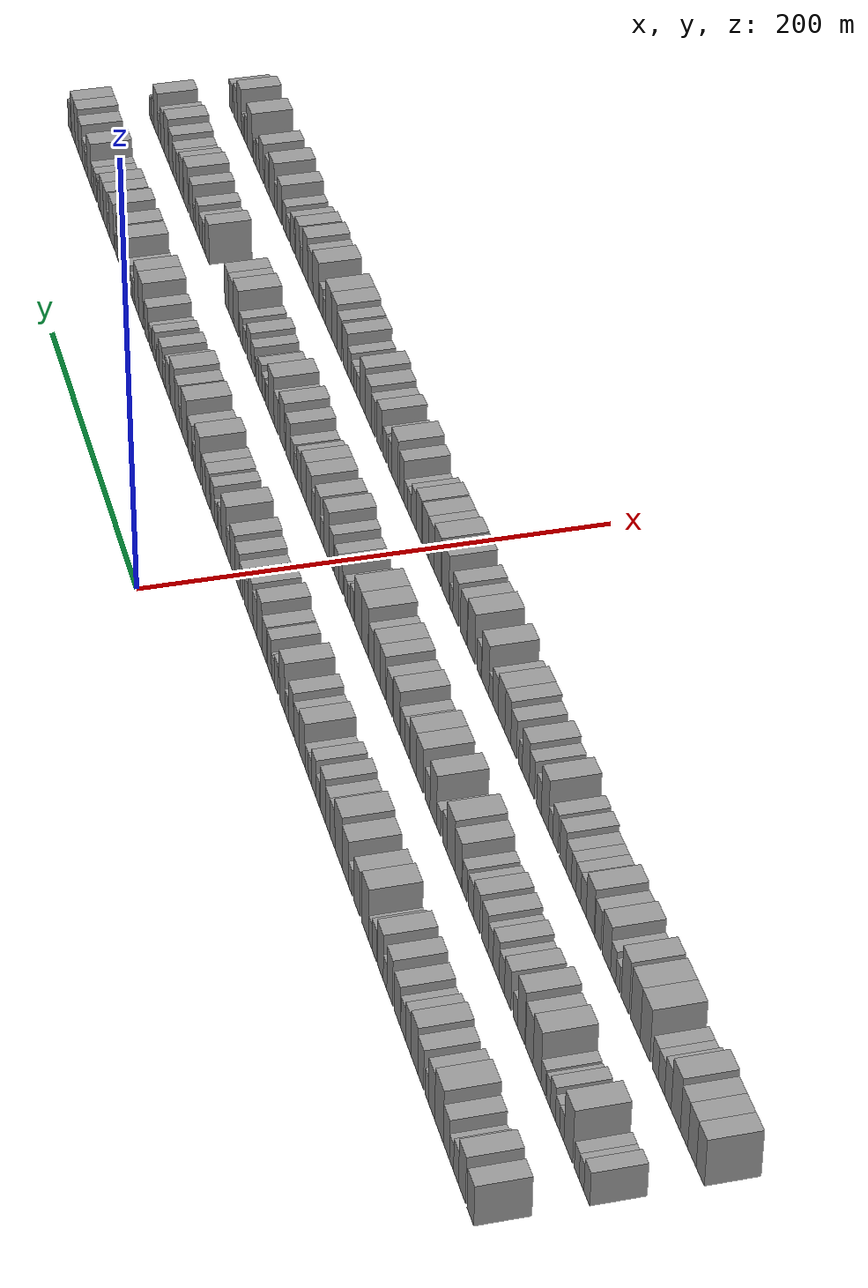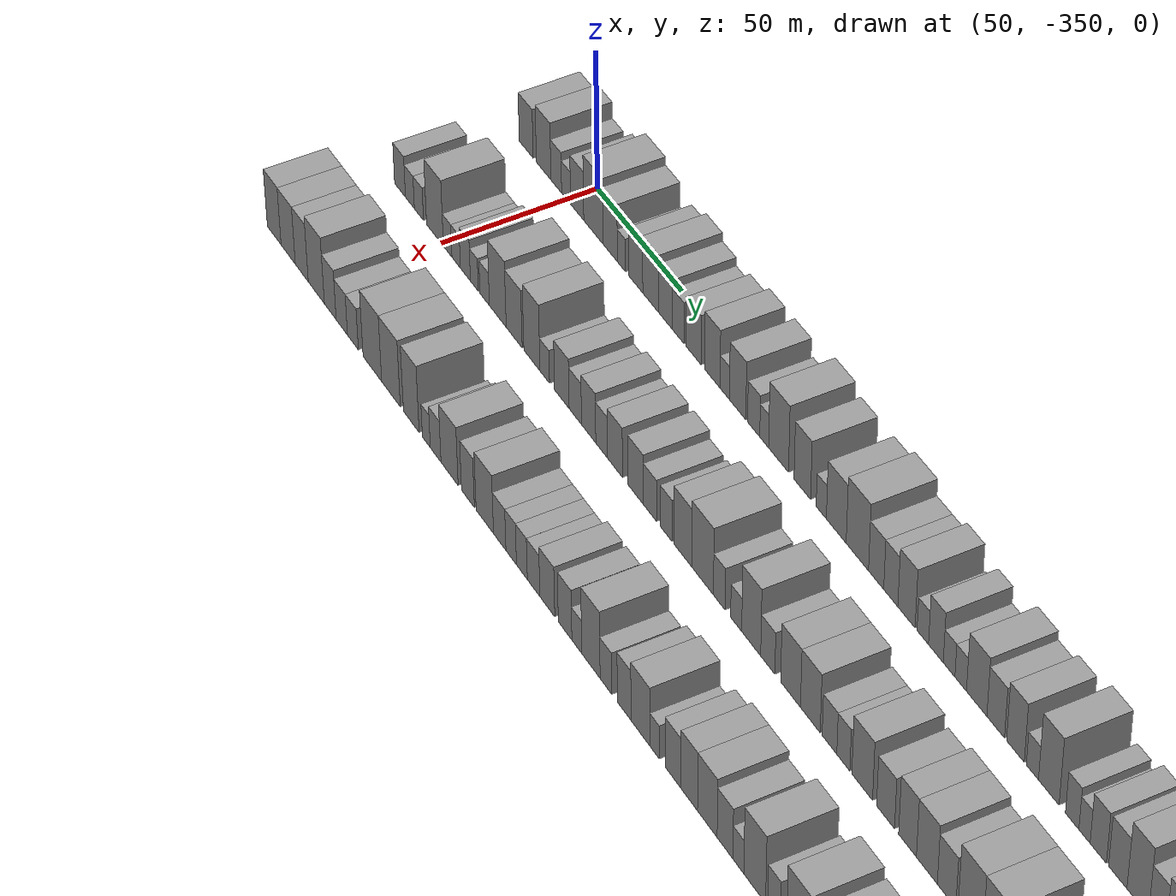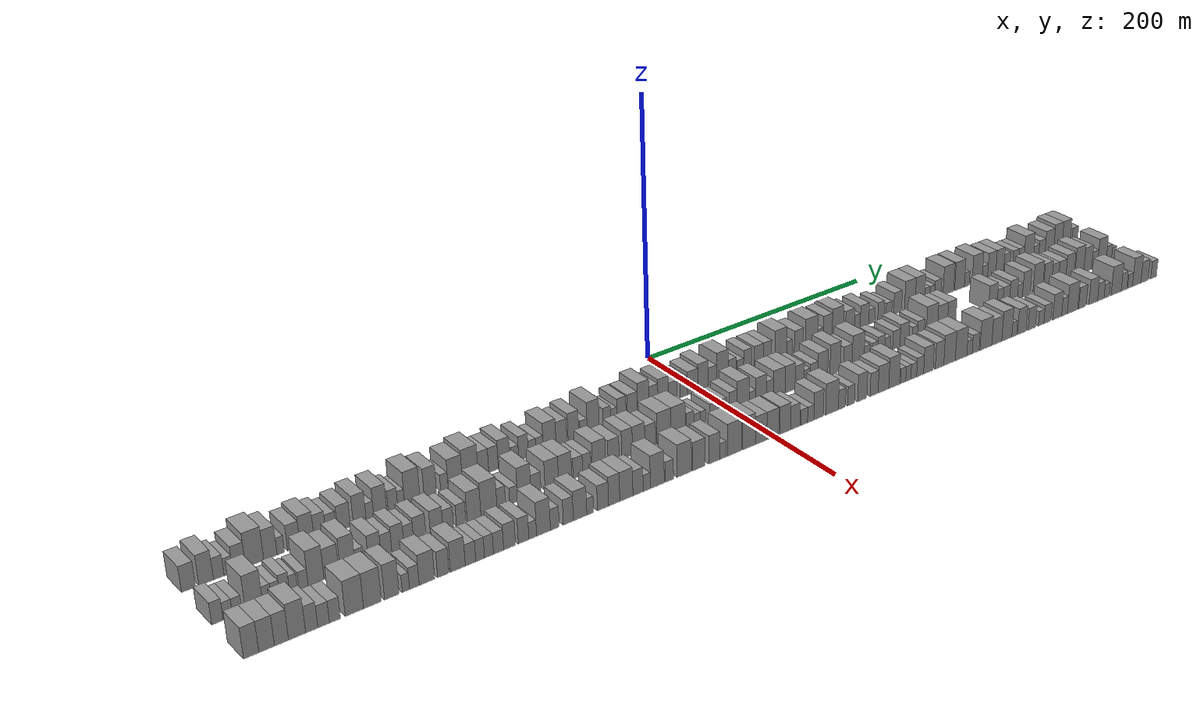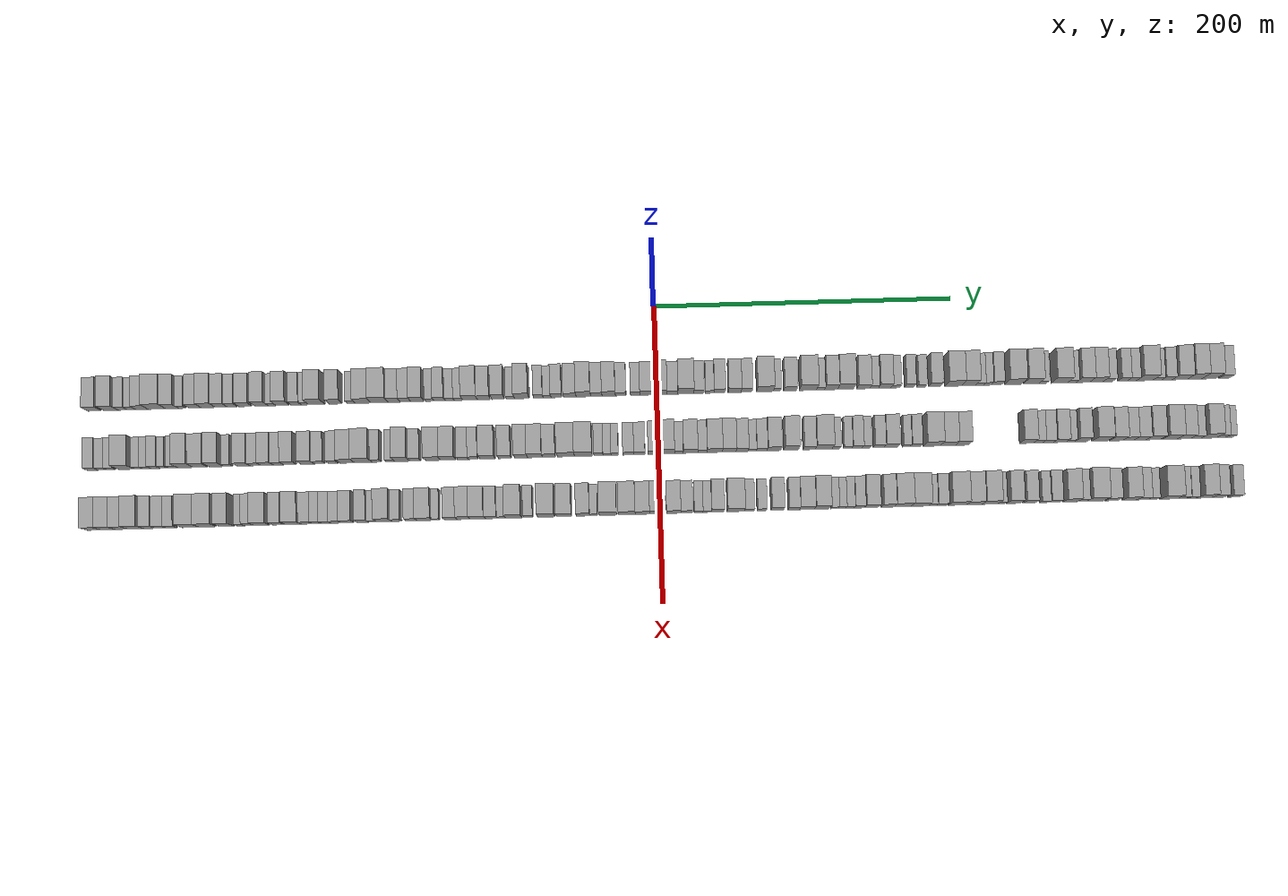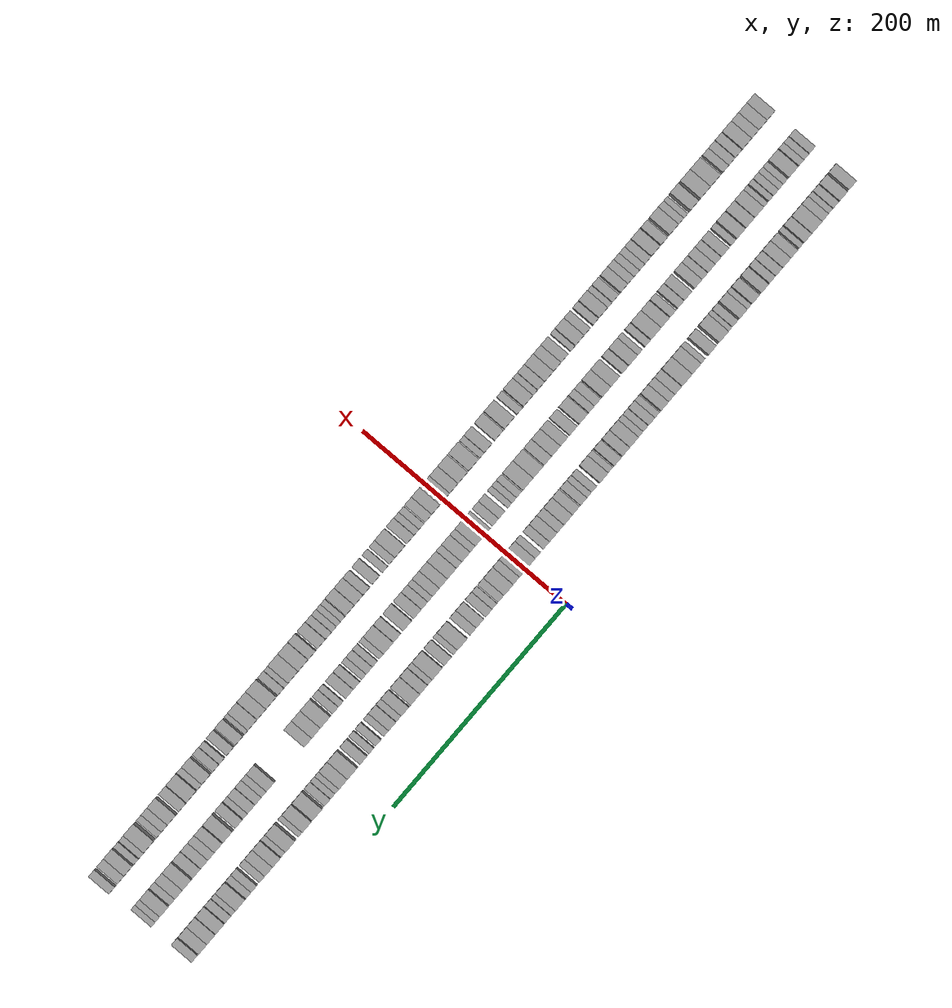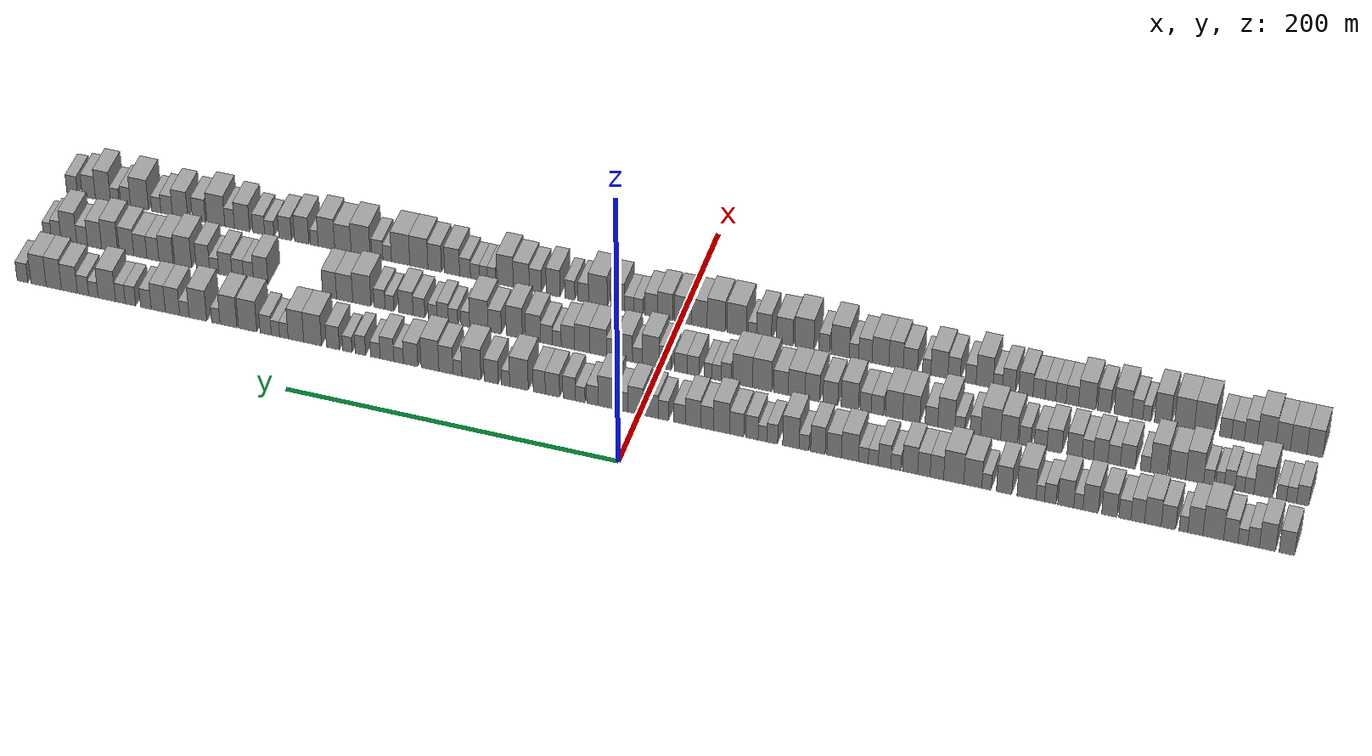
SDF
<sdf version="1.6">
 <world name="default">
  <scene>
   <sky><clouds><speed>12</speed></clouds></sky>
   <ambient>0.4 0.4 0.4 1</ambient>
   <background>0.7 0.7 0.7 1</background>
   <shadows>1</shadows>
  </scene>
  <gravity>0 0 -9.8066</gravity>
  <magnetic_field>6e-06 2.3e-05 -4.2e-05</magnetic_field>
  <physics default="0" name="default_physics" type="ode">
   <ode>
    <solver>
     <type>quick</type>
     <iters>10</iters>
     <sor>1.0</sor>
     <use_dynamic_moi_rescaling>0</use_dynamic_moi_rescaling>
    </solver>
    <constraints>
     <cfm>0</cfm>
     <erp>0.2</erp>
     <contact_max_correcting_vel>100</contact_max_correcting_vel>
     <contact_surface_layer>0.001</contact_surface_layer>
    </constraints>
   </ode>
   <max_step_size>0.004</max_step_size>
   <real_time_factor>1</real_time_factor>
   <real_time_update_rate>250</real_time_update_rate>
  </physics>
  <light name="sun" type="directional">
   <pose>0 0 10 0 0 0</pose>
   <diffuse>0.8 0.8 0.8 1</diffuse>
   <specular>0.2 0.2 0.2 1</specular>
   <attenuation>
    <range>1000</range>
    <constant>0.9</constant>
    <linear>0.01</linear>
    <quadratic>0.001</quadratic>
   </attenuation>
   <direction>-0.5 0.1 -0.9</direction>
  </light>
  <model name="building_1">
   <static>1</static>
   <pose>50.0000 -375.6060 0 0.000000 0.000000 0.000000</pose>
   <link name="link">
    <pose>0 0 9.00 0 0 0</pose>
    <collision name="collision"><geometry><box><size>20.0000 8.7881 18.0000</size></box></geometry></collision>
    <visual name="visual">
     <cast_shadows>0</cast_shadows>
     <geometry><box><size>20.0000 8.7881 18.0000</size></box></geometry>
     <material>
      <script>
       <uri>model://grey_wall/materials/scripts</uri>
       <uri>model://grey_wall/materials/textures</uri>
       <name>vrc/grey_wall</name>
      </script>
     </material>
    </visual>
   </link>
  </model>
  <model name="building_2">
   <static>1</static>
   <pose>50.0000 -364.6403 0 0.000000 0.000000 0.000000</pose>
   <link name="link">
    <pose>0 0 10.50 0 0 0</pose>
    <collision name="collision"><geometry><box><size>20.0000 9.1432 21.0000</size></box></geometry></collision>
    <visual name="visual">
     <cast_shadows>0</cast_shadows>
     <geometry><box><size>20.0000 9.1432 21.0000</size></box></geometry>
     <material>
      <script>
       <uri>model://grey_wall/materials/scripts</uri>
       <uri>model://grey_wall/materials/textures</uri>
       <name>vrc/grey_wall</name>
      </script>
     </material>
    </visual>
   </link>
  </model>
  <model name="building_3">
   <static>1</static>
   <pose>50.0000 -356.7559 0 0.000000 0.000000 0.000000</pose>
   <link name="link">
    <pose>0 0 7.50 0 0 0</pose>
    <collision name="collision"><geometry><box><size>20.0000 6.6256 15.0000</size></box></geometry></collision>
    <visual name="visual">
     <cast_shadows>0</cast_shadows>
     <geometry><box><size>20.0000 6.6256 15.0000</size></box></geometry>
     <material>
      <script>
       <uri>model://grey_wall/materials/scripts</uri>
       <uri>model://grey_wall/materials/textures</uri>
       <name>vrc/grey_wall</name>
      </script>
     </material>
    </visual>
   </link>
  </model>
  <model name="building_4">
   <static>1</static>
   <pose>50.0000 -350.6693 0 0.000000 0.000000 0.000000</pose>
   <link name="link">
    <pose>0 0 6.00 0 0 0</pose>
    <collision name="collision"><geometry><box><size>20.0000 5.5477 12.0000</size></box></geometry></collision>
    <visual name="visual">
     <cast_shadows>0</cast_shadows>
     <geometry><box><size>20.0000 5.5477 12.0000</size></box></geometry>
     <material>
      <script>
       <uri>model://grey_wall/materials/scripts</uri>
       <uri>model://grey_wall/materials/textures</uri>
       <name>vrc/grey_wall</name>
      </script>
     </material>
    </visual>
   </link>
  </model>
  <model name="building_5">
   <static>1</static>
   <pose>50.0000 -343.8528 0 0.000000 0.000000 0.000000</pose>
   <link name="link">
    <pose>0 0 9.00 0 0 0</pose>
    <collision name="collision"><geometry><box><size>20.0000 8.0853 18.0000</size></box></geometry></collision>
    <visual name="visual">
     <cast_shadows>0</cast_shadows>
     <geometry><box><size>20.0000 8.0853 18.0000</size></box></geometry>
     <material>
      <script>
       <uri>model://grey_wall/materials/scripts</uri>
       <uri>model://grey_wall/materials/textures</uri>
       <name>vrc/grey_wall</name>
      </script>
     </material>
    </visual>
   </link>
  </model>
  <model name="building_6">
   <static>1</static>
   <pose>50.0000 -333.9460 0 0.000000 0.000000 0.000000</pose>
   <link name="link">
    <pose>0 0 12.00 0 0 0</pose>
    <collision name="collision"><geometry><box><size>20.0000 11.7281 24.0000</size></box></geometry></collision>
    <visual name="visual">
     <cast_shadows>0</cast_shadows>
     <geometry><box><size>20.0000 11.7281 24.0000</size></box></geometry>
     <material>
      <script>
       <uri>model://grey_wall/materials/scripts</uri>
       <uri>model://grey_wall/materials/textures</uri>
       <name>vrc/grey_wall</name>
      </script>
     </material>
    </visual>
   </link>
  </model>
  <model name="building_7">
   <static>1</static>
   <pose>50.0000 -323.7625 0 0.000000 0.000000 0.000000</pose>
   <link name="link">
    <pose>0 0 10.50 0 0 0</pose>
    <collision name="collision"><geometry><box><size>20.0000 8.6390 21.0000</size></box></geometry></collision>
    <visual name="visual">
     <cast_shadows>0</cast_shadows>
     <geometry><box><size>20.0000 8.6390 21.0000</size></box></geometry>
     <material>
      <script>
       <uri>model://grey_wall/materials/scripts</uri>
       <uri>model://grey_wall/materials/textures</uri>
       <name>vrc/grey_wall</name>
      </script>
     </material>
    </visual>
   </link>
  </model>
  <model name="building_8">
   <static>1</static>
   <pose>50.0000 -317.0072 0 0.000000 0.000000 0.000000</pose>
   <link name="link">
    <pose>0 0 6.00 0 0 0</pose>
    <collision name="collision"><geometry><box><size>20.0000 4.8715 12.0000</size></box></geometry></collision>
    <visual name="visual">
     <cast_shadows>0</cast_shadows>
     <geometry><box><size>20.0000 4.8715 12.0000</size></box></geometry>
     <material>
      <script>
       <uri>model://grey_wall/materials/scripts</uri>
       <uri>model://grey_wall/materials/textures</uri>
       <name>vrc/grey_wall</name>
      </script>
     </material>
    </visual>
   </link>
  </model>
  <model name="building_9">
   <static>1</static>
   <pose>50.0000 -308.4495 0 0.000000 0.000000 0.000000</pose>
   <link name="link">
    <pose>0 0 9.00 0 0 0</pose>
    <collision name="collision"><geometry><box><size>20.0000 8.2440 18.0000</size></box></geometry></collision>
    <visual name="visual">
     <cast_shadows>0</cast_shadows>
     <geometry><box><size>20.0000 8.2440 18.0000</size></box></geometry>
     <material>
      <script>
       <uri>model://grey_wall/materials/scripts</uri>
       <uri>model://grey_wall/materials/textures</uri>
       <name>vrc/grey_wall</name>
      </script>
     </material>
    </visual>
   </link>
  </model>
  <model name="building_10">
   <static>1</static>
   <pose>50.0000 -299.6139 0 0.000000 0.000000 0.000000</pose>
   <link name="link">
    <pose>0 0 10.50 0 0 0</pose>
    <collision name="collision"><geometry><box><size>20.0000 9.4271 21.0000</size></box></geometry></collision>
    <visual name="visual">
     <cast_shadows>0</cast_shadows>
     <geometry><box><size>20.0000 9.4271 21.0000</size></box></geometry>
     <material>
      <script>
       <uri>model://grey_wall/materials/scripts</uri>
       <uri>model://grey_wall/materials/textures</uri>
       <name>vrc/grey_wall</name>
      </script>
     </material>
    </visual>
   </link>
  </model>
  <model name="building_11">
   <static>1</static>
   <pose>50.0000 -290.9620 0 0.000000 0.000000 0.000000</pose>
   <link name="link">
    <pose>0 0 9.00 0 0 0</pose>
    <collision name="collision"><geometry><box><size>20.0000 7.8766 18.0000</size></box></geometry></collision>
    <visual name="visual">
     <cast_shadows>0</cast_shadows>
     <geometry><box><size>20.0000 7.8766 18.0000</size></box></geometry>
     <material>
      <script>
       <uri>model://grey_wall/materials/scripts</uri>
       <uri>model://grey_wall/materials/textures</uri>
       <name>vrc/grey_wall</name>
      </script>
     </material>
    </visual>
   </link>
  </model>
  <model name="building_12">
   <static>1</static>
   <pose>50.0000 -283.6015 0 0.000000 0.000000 0.000000</pose>
   <link name="link">
    <pose>0 0 7.50 0 0 0</pose>
    <collision name="collision"><geometry><box><size>20.0000 6.8444 15.0000</size></box></geometry></collision>
    <visual name="visual">
     <cast_shadows>0</cast_shadows>
     <geometry><box><size>20.0000 6.8444 15.0000</size></box></geometry>
     <material>
      <script>
       <uri>model://grey_wall/materials/scripts</uri>
       <uri>model://grey_wall/materials/textures</uri>
       <name>vrc/grey_wall</name>
      </script>
     </material>
    </visual>
   </link>
  </model>
  <model name="building_13">
   <static>1</static>
   <pose>50.0000 -274.7930 0 0.000000 0.000000 0.000000</pose>
   <link name="link">
    <pose>0 0 9.00 0 0 0</pose>
    <collision name="collision"><geometry><box><size>20.0000 8.7725 18.0000</size></box></geometry></collision>
    <visual name="visual">
     <cast_shadows>0</cast_shadows>
     <geometry><box><size>20.0000 8.7725 18.0000</size></box></geometry>
     <material>
      <script>
       <uri>model://grey_wall/materials/scripts</uri>
       <uri>model://grey_wall/materials/textures</uri>
       <name>vrc/grey_wall</name>
      </script>
     </material>
    </visual>
   </link>
  </model>
  <model name="building_14">
   <static>1</static>
   <pose>50.0000 -264.0274 0 0.000000 0.000000 0.000000</pose>
   <link name="link">
    <pose>0 0 10.50 0 0 0</pose>
    <collision name="collision"><geometry><box><size>20.0000 8.7588 21.0000</size></box></geometry></collision>
    <visual name="visual">
     <cast_shadows>0</cast_shadows>
     <geometry><box><size>20.0000 8.7588 21.0000</size></box></geometry>
     <material>
      <script>
       <uri>model://grey_wall/materials/scripts</uri>
       <uri>model://grey_wall/materials/textures</uri>
       <name>vrc/grey_wall</name>
      </script>
     </material>
    </visual>
   </link>
  </model>
  <model name="building_15">
   <static>1</static>
   <pose>50.0000 -257.0057 0 0.000000 0.000000 0.000000</pose>
   <link name="link">
    <pose>0 0 6.00 0 0 0</pose>
    <collision name="collision"><geometry><box><size>20.0000 5.2845 12.0000</size></box></geometry></collision>
    <visual name="visual">
     <cast_shadows>0</cast_shadows>
     <geometry><box><size>20.0000 5.2845 12.0000</size></box></geometry>
     <material>
      <script>
       <uri>model://grey_wall/materials/scripts</uri>
       <uri>model://grey_wall/materials/textures</uri>
       <name>vrc/grey_wall</name>
      </script>
     </material>
    </visual>
   </link>
  </model>
  <model name="building_16">
   <static>1</static>
   <pose>50.0000 -249.7945 0 0.000000 0.000000 0.000000</pose>
   <link name="link">
    <pose>0 0 10.50 0 0 0</pose>
    <collision name="collision"><geometry><box><size>20.0000 9.1378 21.0000</size></box></geometry></collision>
    <visual name="visual">
     <cast_shadows>0</cast_shadows>
     <geometry><box><size>20.0000 9.1378 21.0000</size></box></geometry>
     <material>
      <script>
       <uri>model://grey_wall/materials/scripts</uri>
       <uri>model://grey_wall/materials/textures</uri>
       <name>vrc/grey_wall</name>
      </script>
     </material>
    </visual>
   </link>
  </model>
  <model name="building_17">
   <static>1</static>
   <pose>50.0000 -240.8552 0 0.000000 0.000000 0.000000</pose>
   <link name="link">
    <pose>0 0 7.50 0 0 0</pose>
    <collision name="collision"><geometry><box><size>20.0000 6.7409 15.0000</size></box></geometry></collision>
    <visual name="visual">
     <cast_shadows>0</cast_shadows>
     <geometry><box><size>20.0000 6.7409 15.0000</size></box></geometry>
     <material>
      <script>
       <uri>model://grey_wall/materials/scripts</uri>
       <uri>model://grey_wall/materials/textures</uri>
       <name>vrc/grey_wall</name>
      </script>
     </material>
    </visual>
   </link>
  </model>
  <model name="building_18">
   <static>1</static>
   <pose>50.0000 -235.0517 0 0.000000 0.000000 0.000000</pose>
   <link name="link">
    <pose>0 0 6.00 0 0 0</pose>
    <collision name="collision"><geometry><box><size>20.0000 4.8660 12.0000</size></box></geometry></collision>
    <visual name="visual">
     <cast_shadows>0</cast_shadows>
     <geometry><box><size>20.0000 4.8660 12.0000</size></box></geometry>
     <material>
      <script>
       <uri>model://grey_wall/materials/scripts</uri>
       <uri>model://grey_wall/materials/textures</uri>
       <name>vrc/grey_wall</name>
      </script>
     </material>
    </visual>
   </link>
  </model>
  <model name="building_19">
   <static>1</static>
   <pose>50.0000 -227.1657 0 0.000000 0.000000 0.000000</pose>
   <link name="link">
    <pose>0 0 12.00 0 0 0</pose>
    <collision name="collision"><geometry><box><size>20.0000 10.9060 24.0000</size></box></geometry></collision>
    <visual name="visual">
     <cast_shadows>0</cast_shadows>
     <geometry><box><size>20.0000 10.9060 24.0000</size></box></geometry>
     <material>
      <script>
       <uri>model://grey_wall/materials/scripts</uri>
       <uri>model://grey_wall/materials/textures</uri>
       <name>vrc/grey_wall</name>
      </script>
     </material>
    </visual>
   </link>
  </model>
  <model name="building_20">
   <static>1</static>
   <pose>50.0000 -214.2482 0 0.000000 0.000000 0.000000</pose>
   <link name="link">
    <pose>0 0 10.50 0 0 0</pose>
    <collision name="collision"><geometry><box><size>20.0000 8.9290 21.0000</size></box></geometry></collision>
    <visual name="visual">
     <cast_shadows>0</cast_shadows>
     <geometry><box><size>20.0000 8.9290 21.0000</size></box></geometry>
     <material>
      <script>
       <uri>model://grey_wall/materials/scripts</uri>
       <uri>model://grey_wall/materials/textures</uri>
       <name>vrc/grey_wall</name>
      </script>
     </material>
    </visual>
   </link>
  </model>
  <model name="building_21">
   <static>1</static>
   <pose>50.0000 -204.0653 0 0.000000 0.000000 0.000000</pose>
   <link name="link">
    <pose>0 0 6.00 0 0 0</pose>
    <collision name="collision"><geometry><box><size>20.0000 5.4369 12.0000</size></box></geometry></collision>
    <visual name="visual">
     <cast_shadows>0</cast_shadows>
     <geometry><box><size>20.0000 5.4369 12.0000</size></box></geometry>
     <material>
      <script>
       <uri>model://grey_wall/materials/scripts</uri>
       <uri>model://grey_wall/materials/textures</uri>
       <name>vrc/grey_wall</name>
      </script>
     </material>
    </visual>
   </link>
  </model>
  <model name="building_22">
   <static>1</static>
   <pose>50.0000 -196.1051 0 0.000000 0.000000 0.000000</pose>
   <link name="link">
    <pose>0 0 10.50 0 0 0</pose>
    <collision name="collision"><geometry><box><size>20.0000 10.4834 21.0000</size></box></geometry></collision>
    <visual name="visual">
     <cast_shadows>0</cast_shadows>
     <geometry><box><size>20.0000 10.4834 21.0000</size></box></geometry>
     <material>
      <script>
       <uri>model://grey_wall/materials/scripts</uri>
       <uri>model://grey_wall/materials/textures</uri>
       <name>vrc/grey_wall</name>
      </script>
     </material>
    </visual>
   </link>
  </model>
  <model name="building_23">
   <static>1</static>
   <pose>50.0000 -185.0054 0 0.000000 0.000000 0.000000</pose>
   <link name="link">
    <pose>0 0 12.00 0 0 0</pose>
    <collision name="collision"><geometry><box><size>20.0000 11.7162 24.0000</size></box></geometry></collision>
    <visual name="visual">
     <cast_shadows>0</cast_shadows>
     <geometry><box><size>20.0000 11.7162 24.0000</size></box></geometry>
     <material>
      <script>
       <uri>model://grey_wall/materials/scripts</uri>
       <uri>model://grey_wall/materials/textures</uri>
       <name>vrc/grey_wall</name>
      </script>
     </material>
    </visual>
   </link>
  </model>
  <model name="building_24">
   <static>1</static>
   <pose>50.0000 -175.2035 0 0.000000 0.000000 0.000000</pose>
   <link name="link">
    <pose>0 0 9.00 0 0 0</pose>
    <collision name="collision"><geometry><box><size>20.0000 7.8875 18.0000</size></box></geometry></collision>
    <visual name="visual">
     <cast_shadows>0</cast_shadows>
     <geometry><box><size>20.0000 7.8875 18.0000</size></box></geometry>
     <material>
      <script>
       <uri>model://grey_wall/materials/scripts</uri>
       <uri>model://grey_wall/materials/textures</uri>
       <name>vrc/grey_wall</name>
      </script>
     </material>
    </visual>
   </link>
  </model>
  <model name="building_25">
   <static>1</static>
   <pose>50.0000 -167.6401 0 0.000000 0.000000 0.000000</pose>
   <link name="link">
    <pose>0 0 9.00 0 0 0</pose>
    <collision name="collision"><geometry><box><size>20.0000 7.2393 18.0000</size></box></geometry></collision>
    <visual name="visual">
     <cast_shadows>0</cast_shadows>
     <geometry><box><size>20.0000 7.2393 18.0000</size></box></geometry>
     <material>
      <script>
       <uri>model://grey_wall/materials/scripts</uri>
       <uri>model://grey_wall/materials/textures</uri>
       <name>vrc/grey_wall</name>
      </script>
     </material>
    </visual>
   </link>
  </model>
  <model name="building_26">
   <static>1</static>
   <pose>50.0000 -159.6089 0 0.000000 0.000000 0.000000</pose>
   <link name="link">
    <pose>0 0 10.50 0 0 0</pose>
    <collision name="collision"><geometry><box><size>20.0000 8.8232 21.0000</size></box></geometry></collision>
    <visual name="visual">
     <cast_shadows>0</cast_shadows>
     <geometry><box><size>20.0000 8.8232 21.0000</size></box></geometry>
     <material>
      <script>
       <uri>model://grey_wall/materials/scripts</uri>
       <uri>model://grey_wall/materials/textures</uri>
       <name>vrc/grey_wall</name>
      </script>
     </material>
    </visual>
   </link>
  </model>
  <model name="building_27">
   <static>1</static>
   <pose>50.0000 -151.3095 0 0.000000 0.000000 0.000000</pose>
   <link name="link">
    <pose>0 0 6.00 0 0 0</pose>
    <collision name="collision"><geometry><box><size>20.0000 5.7755 12.0000</size></box></geometry></collision>
    <visual name="visual">
     <cast_shadows>0</cast_shadows>
     <geometry><box><size>20.0000 5.7755 12.0000</size></box></geometry>
     <material>
      <script>
       <uri>model://grey_wall/materials/scripts</uri>
       <uri>model://grey_wall/materials/textures</uri>
       <name>vrc/grey_wall</name>
      </script>
     </material>
    </visual>
   </link>
  </model>
  <model name="building_28">
   <static>1</static>
   <pose>50.0000 -144.7260 0 0.000000 0.000000 0.000000</pose>
   <link name="link">
    <pose>0 0 9.00 0 0 0</pose>
    <collision name="collision"><geometry><box><size>20.0000 7.3917 18.0000</size></box></geometry></collision>
    <visual name="visual">
     <cast_shadows>0</cast_shadows>
     <geometry><box><size>20.0000 7.3917 18.0000</size></box></geometry>
     <material>
      <script>
       <uri>model://grey_wall/materials/scripts</uri>
       <uri>model://grey_wall/materials/textures</uri>
       <name>vrc/grey_wall</name>
      </script>
     </material>
    </visual>
   </link>
  </model>
  <model name="building_29">
   <static>1</static>
   <pose>50.0000 -138.1124 0 0.000000 0.000000 0.000000</pose>
   <link name="link">
    <pose>0 0 6.00 0 0 0</pose>
    <collision name="collision"><geometry><box><size>20.0000 5.8354 12.0000</size></box></geometry></collision>
    <visual name="visual">
     <cast_shadows>0</cast_shadows>
     <geometry><box><size>20.0000 5.8354 12.0000</size></box></geometry>
     <material>
      <script>
       <uri>model://grey_wall/materials/scripts</uri>
       <uri>model://grey_wall/materials/textures</uri>
       <name>vrc/grey_wall</name>
      </script>
     </material>
    </visual>
   </link>
  </model>
  <model name="building_30">
   <static>1</static>
   <pose>50.0000 -132.3395 0 0.000000 0.000000 0.000000</pose>
   <link name="link">
    <pose>0 0 6.00 0 0 0</pose>
    <collision name="collision"><geometry><box><size>20.0000 5.7104 12.0000</size></box></geometry></collision>
    <visual name="visual">
     <cast_shadows>0</cast_shadows>
     <geometry><box><size>20.0000 5.7104 12.0000</size></box></geometry>
     <material>
      <script>
       <uri>model://grey_wall/materials/scripts</uri>
       <uri>model://grey_wall/materials/textures</uri>
       <name>vrc/grey_wall</name>
      </script>
     </material>
    </visual>
   </link>
  </model>
  <model name="building_31">
   <static>1</static>
   <pose>50.0000 -124.4697 0 0.000000 0.000000 0.000000</pose>
   <link name="link">
    <pose>0 0 10.50 0 0 0</pose>
    <collision name="collision"><geometry><box><size>20.0000 10.0291 21.0000</size></box></geometry></collision>
    <visual name="visual">
     <cast_shadows>0</cast_shadows>
     <geometry><box><size>20.0000 10.0291 21.0000</size></box></geometry>
     <material>
      <script>
       <uri>model://grey_wall/materials/scripts</uri>
       <uri>model://grey_wall/materials/textures</uri>
       <name>vrc/grey_wall</name>
      </script>
     </material>
    </visual>
   </link>
  </model>
  <model name="building_32">
   <static>1</static>
   <pose>50.0000 -115.1721 0 0.000000 0.000000 0.000000</pose>
   <link name="link">
    <pose>0 0 9.00 0 0 0</pose>
    <collision name="collision"><geometry><box><size>20.0000 8.5661 18.0000</size></box></geometry></collision>
    <visual name="visual">
     <cast_shadows>0</cast_shadows>
     <geometry><box><size>20.0000 8.5661 18.0000</size></box></geometry>
     <material>
      <script>
       <uri>model://grey_wall/materials/scripts</uri>
       <uri>model://grey_wall/materials/textures</uri>
       <name>vrc/grey_wall</name>
      </script>
     </material>
    </visual>
   </link>
  </model>
  <model name="building_33">
   <static>1</static>
   <pose>50.0000 -105.6308 0 0.000000 0.000000 0.000000</pose>
   <link name="link">
    <pose>0 0 10.50 0 0 0</pose>
    <collision name="collision"><geometry><box><size>20.0000 8.5166 21.0000</size></box></geometry></collision>
    <visual name="visual">
     <cast_shadows>0</cast_shadows>
     <geometry><box><size>20.0000 8.5166 21.0000</size></box></geometry>
     <material>
      <script>
       <uri>model://grey_wall/materials/scripts</uri>
       <uri>model://grey_wall/materials/textures</uri>
       <name>vrc/grey_wall</name>
      </script>
     </material>
    </visual>
   </link>
  </model>
  <model name="building_34">
   <static>1</static>
   <pose>50.0000 -97.4815 0 0.000000 0.000000 0.000000</pose>
   <link name="link">
    <pose>0 0 6.00 0 0 0</pose>
    <collision name="collision"><geometry><box><size>20.0000 5.7820 12.0000</size></box></geometry></collision>
    <visual name="visual">
     <cast_shadows>0</cast_shadows>
     <geometry><box><size>20.0000 5.7820 12.0000</size></box></geometry>
     <material>
      <script>
       <uri>model://grey_wall/materials/scripts</uri>
       <uri>model://grey_wall/materials/textures</uri>
       <name>vrc/grey_wall</name>
      </script>
     </material>
    </visual>
   </link>
  </model>
  <model name="building_35">
   <static>1</static>
   <pose>50.0000 -89.7248 0 0.000000 0.000000 0.000000</pose>
   <link name="link">
    <pose>0 0 12.00 0 0 0</pose>
    <collision name="collision"><geometry><box><size>20.0000 9.7313 24.0000</size></box></geometry></collision>
    <visual name="visual">
     <cast_shadows>0</cast_shadows>
     <geometry><box><size>20.0000 9.7313 24.0000</size></box></geometry>
     <material>
      <script>
       <uri>model://grey_wall/materials/scripts</uri>
       <uri>model://grey_wall/materials/textures</uri>
       <name>vrc/grey_wall</name>
      </script>
     </material>
    </visual>
   </link>
  </model>
  <model name="building_36">
   <static>1</static>
   <pose>50.0000 -78.7256 0 0.000000 0.000000 0.000000</pose>
   <link name="link">
    <pose>0 0 7.50 0 0 0</pose>
    <collision name="collision"><geometry><box><size>20.0000 6.2670 15.0000</size></box></geometry></collision>
    <visual name="visual">
     <cast_shadows>0</cast_shadows>
     <geometry><box><size>20.0000 6.2670 15.0000</size></box></geometry>
     <material>
      <script>
       <uri>model://grey_wall/materials/scripts</uri>
       <uri>model://grey_wall/materials/textures</uri>
       <name>vrc/grey_wall</name>
      </script>
     </material>
    </visual>
   </link>
  </model>
  <model name="building_37">
   <static>1</static>
   <pose>50.0000 -72.9739 0 0.000000 0.000000 0.000000</pose>
   <link name="link">
    <pose>0 0 6.00 0 0 0</pose>
    <collision name="collision"><geometry><box><size>20.0000 5.2365 12.0000</size></box></geometry></collision>
    <visual name="visual">
     <cast_shadows>0</cast_shadows>
     <geometry><box><size>20.0000 5.2365 12.0000</size></box></geometry>
     <material>
      <script>
       <uri>model://grey_wall/materials/scripts</uri>
       <uri>model://grey_wall/materials/textures</uri>
       <name>vrc/grey_wall</name>
      </script>
     </material>
    </visual>
   </link>
  </model>
  <model name="building_38">
   <static>1</static>
   <pose>50.0000 -66.6199 0 0.000000 0.000000 0.000000</pose>
   <link name="link">
    <pose>0 0 9.00 0 0 0</pose>
    <collision name="collision"><geometry><box><size>20.0000 7.4715 18.0000</size></box></geometry></collision>
    <visual name="visual">
     <cast_shadows>0</cast_shadows>
     <geometry><box><size>20.0000 7.4715 18.0000</size></box></geometry>
     <material>
      <script>
       <uri>model://grey_wall/materials/scripts</uri>
       <uri>model://grey_wall/materials/textures</uri>
       <name>vrc/grey_wall</name>
      </script>
     </material>
    </visual>
   </link>
  </model>
  <model name="building_39">
   <static>1</static>
   <pose>50.0000 -57.6942 0 0.000000 0.000000 0.000000</pose>
   <link name="link">
    <pose>0 0 9.00 0 0 0</pose>
    <collision name="collision"><geometry><box><size>20.0000 8.3799 18.0000</size></box></geometry></collision>
    <visual name="visual">
     <cast_shadows>0</cast_shadows>
     <geometry><box><size>20.0000 8.3799 18.0000</size></box></geometry>
     <material>
      <script>
       <uri>model://grey_wall/materials/scripts</uri>
       <uri>model://grey_wall/materials/textures</uri>
       <name>vrc/grey_wall</name>
      </script>
     </material>
    </visual>
   </link>
  </model>
  <model name="building_40">
   <static>1</static>
   <pose>50.0000 -48.6485 0 0.000000 0.000000 0.000000</pose>
   <link name="link">
    <pose>0 0 12.00 0 0 0</pose>
    <collision name="collision"><geometry><box><size>20.0000 9.7114 24.0000</size></box></geometry></collision>
    <visual name="visual">
     <cast_shadows>0</cast_shadows>
     <geometry><box><size>20.0000 9.7114 24.0000</size></box></geometry>
     <material>
      <script>
       <uri>model://grey_wall/materials/scripts</uri>
       <uri>model://grey_wall/materials/textures</uri>
       <name>vrc/grey_wall</name>
      </script>
     </material>
    </visual>
   </link>
  </model>
  <model name="building_41">
   <static>1</static>
   <pose>50.0000 -39.9745 0 0.000000 0.000000 0.000000</pose>
   <link name="link">
    <pose>0 0 9.00 0 0 0</pose>
    <collision name="collision"><geometry><box><size>20.0000 7.6367 18.0000</size></box></geometry></collision>
    <visual name="visual">
     <cast_shadows>0</cast_shadows>
     <geometry><box><size>20.0000 7.6367 18.0000</size></box></geometry>
     <material>
      <script>
       <uri>model://grey_wall/materials/scripts</uri>
       <uri>model://grey_wall/materials/textures</uri>
       <name>vrc/grey_wall</name>
      </script>
     </material>
    </visual>
   </link>
  </model>
  <model name="building_42">
   <static>1</static>
   <pose>50.0000 -31.7068 0 0.000000 0.000000 0.000000</pose>
   <link name="link">
    <pose>0 0 10.50 0 0 0</pose>
    <collision name="collision"><geometry><box><size>20.0000 8.8987 21.0000</size></box></geometry></collision>
    <visual name="visual">
     <cast_shadows>0</cast_shadows>
     <geometry><box><size>20.0000 8.8987 21.0000</size></box></geometry>
     <material>
      <script>
       <uri>model://grey_wall/materials/scripts</uri>
       <uri>model://grey_wall/materials/textures</uri>
       <name>vrc/grey_wall</name>
      </script>
     </material>
    </visual>
   </link>
  </model>
  <model name="building_43">
   <static>1</static>
   <pose>50.0000 -23.6906 0 0.000000 0.000000 0.000000</pose>
   <link name="link">
    <pose>0 0 7.50 0 0 0</pose>
    <collision name="collision"><geometry><box><size>20.0000 7.1337 15.0000</size></box></geometry></collision>
    <visual name="visual">
     <cast_shadows>0</cast_shadows>
     <geometry><box><size>20.0000 7.1337 15.0000</size></box></geometry>
     <material>
      <script>
       <uri>model://grey_wall/materials/scripts</uri>
       <uri>model://grey_wall/materials/textures</uri>
       <name>vrc/grey_wall</name>
      </script>
     </material>
    </visual>
   </link>
  </model>
  <model name="building_44">
   <static>1</static>
   <pose>50.0000 -14.0508 0 0.000000 0.000000 0.000000</pose>
   <link name="link">
    <pose>0 0 7.50 0 0 0</pose>
    <collision name="collision"><geometry><box><size>20.0000 6.1459 15.0000</size></box></geometry></collision>
    <visual name="visual">
     <cast_shadows>0</cast_shadows>
     <geometry><box><size>20.0000 6.1459 15.0000</size></box></geometry>
     <material>
      <script>
       <uri>model://grey_wall/materials/scripts</uri>
       <uri>model://grey_wall/materials/textures</uri>
       <name>vrc/grey_wall</name>
      </script>
     </material>
    </visual>
   </link>
  </model>
  <model name="building_45">
   <static>1</static>
   <pose>50.0000 -6.4966 0 0.000000 0.000000 0.000000</pose>
   <link name="link">
    <pose>0 0 9.00 0 0 0</pose>
    <collision name="collision"><geometry><box><size>20.0000 8.9625 18.0000</size></box></geometry></collision>
    <visual name="visual">
     <cast_shadows>0</cast_shadows>
     <geometry><box><size>20.0000 8.9625 18.0000</size></box></geometry>
     <material>
      <script>
       <uri>model://grey_wall/materials/scripts</uri>
       <uri>model://grey_wall/materials/textures</uri>
       <name>vrc/grey_wall</name>
      </script>
     </material>
    </visual>
   </link>
  </model>
  <model name="building_46">
   <static>1</static>
   <pose>50.0000 2.6017 0 0.000000 0.000000 0.000000</pose>
   <link name="link">
    <pose>0 0 10.50 0 0 0</pose>
    <collision name="collision"><geometry><box><size>20.0000 9.2339 21.0000</size></box></geometry></collision>
    <visual name="visual">
     <cast_shadows>0</cast_shadows>
     <geometry><box><size>20.0000 9.2339 21.0000</size></box></geometry>
     <material>
      <script>
       <uri>model://grey_wall/materials/scripts</uri>
       <uri>model://grey_wall/materials/textures</uri>
       <name>vrc/grey_wall</name>
      </script>
     </material>
    </visual>
   </link>
  </model>
  <model name="building_47">
   <static>1</static>
   <pose>50.0000 10.8384 0 0.000000 0.000000 0.000000</pose>
   <link name="link">
    <pose>0 0 7.50 0 0 0</pose>
    <collision name="collision"><geometry><box><size>20.0000 7.2396 15.0000</size></box></geometry></collision>
    <visual name="visual">
     <cast_shadows>0</cast_shadows>
     <geometry><box><size>20.0000 7.2396 15.0000</size></box></geometry>
     <material>
      <script>
       <uri>model://grey_wall/materials/scripts</uri>
       <uri>model://grey_wall/materials/textures</uri>
       <name>vrc/grey_wall</name>
      </script>
     </material>
    </visual>
   </link>
  </model>
  <model name="building_48">
   <static>1</static>
   <pose>50.0000 19.7952 0 0.000000 0.000000 0.000000</pose>
   <link name="link">
    <pose>0 0 12.00 0 0 0</pose>
    <collision name="collision"><geometry><box><size>20.0000 10.6739 24.0000</size></box></geometry></collision>
    <visual name="visual">
     <cast_shadows>0</cast_shadows>
     <geometry><box><size>20.0000 10.6739 24.0000</size></box></geometry>
     <material>
      <script>
       <uri>model://grey_wall/materials/scripts</uri>
       <uri>model://grey_wall/materials/textures</uri>
       <name>vrc/grey_wall</name>
      </script>
     </material>
    </visual>
   </link>
  </model>
  <model name="building_49">
   <static>1</static>
   <pose>50.0000 28.5236 0 0.000000 0.000000 0.000000</pose>
   <link name="link">
    <pose>0 0 7.50 0 0 0</pose>
    <collision name="collision"><geometry><box><size>20.0000 6.7829 15.0000</size></box></geometry></collision>
    <visual name="visual">
     <cast_shadows>0</cast_shadows>
     <geometry><box><size>20.0000 6.7829 15.0000</size></box></geometry>
     <material>
      <script>
       <uri>model://grey_wall/materials/scripts</uri>
       <uri>model://grey_wall/materials/textures</uri>
       <name>vrc/grey_wall</name>
      </script>
     </material>
    </visual>
   </link>
  </model>
  <model name="building_50">
   <static>1</static>
   <pose>50.0000 35.7836 0 0.000000 0.000000 0.000000</pose>
   <link name="link">
    <pose>0 0 6.00 0 0 0</pose>
    <collision name="collision"><geometry><box><size>20.0000 5.7371 12.0000</size></box></geometry></collision>
    <visual name="visual">
     <cast_shadows>0</cast_shadows>
     <geometry><box><size>20.0000 5.7371 12.0000</size></box></geometry>
     <material>
      <script>
       <uri>model://grey_wall/materials/scripts</uri>
       <uri>model://grey_wall/materials/textures</uri>
       <name>vrc/grey_wall</name>
      </script>
     </material>
    </visual>
   </link>
  </model>
  <model name="building_51">
   <static>1</static>
   <pose>50.0000 42.4287 0 0.000000 0.000000 0.000000</pose>
   <link name="link">
    <pose>0 0 9.00 0 0 0</pose>
    <collision name="collision"><geometry><box><size>20.0000 7.5531 18.0000</size></box></geometry></collision>
    <visual name="visual">
     <cast_shadows>0</cast_shadows>
     <geometry><box><size>20.0000 7.5531 18.0000</size></box></geometry>
     <material>
      <script>
       <uri>model://grey_wall/materials/scripts</uri>
       <uri>model://grey_wall/materials/textures</uri>
       <name>vrc/grey_wall</name>
      </script>
     </material>
    </visual>
   </link>
  </model>
  <model name="building_52">
   <static>1</static>
   <pose>50.0000 52.5338 0 0.000000 0.000000 0.000000</pose>
   <link name="link">
    <pose>0 0 9.00 0 0 0</pose>
    <collision name="collision"><geometry><box><size>20.0000 8.6570 18.0000</size></box></geometry></collision>
    <visual name="visual">
     <cast_shadows>0</cast_shadows>
     <geometry><box><size>20.0000 8.6570 18.0000</size></box></geometry>
     <material>
      <script>
       <uri>model://grey_wall/materials/scripts</uri>
       <uri>model://grey_wall/materials/textures</uri>
       <name>vrc/grey_wall</name>
      </script>
     </material>
    </visual>
   </link>
  </model>
  <model name="building_53">
   <static>1</static>
   <pose>50.0000 60.5032 0 0.000000 0.000000 0.000000</pose>
   <link name="link">
    <pose>0 0 9.00 0 0 0</pose>
    <collision name="collision"><geometry><box><size>20.0000 7.2819 18.0000</size></box></geometry></collision>
    <visual name="visual">
     <cast_shadows>0</cast_shadows>
     <geometry><box><size>20.0000 7.2819 18.0000</size></box></geometry>
     <material>
      <script>
       <uri>model://grey_wall/materials/scripts</uri>
       <uri>model://grey_wall/materials/textures</uri>
       <name>vrc/grey_wall</name>
      </script>
     </material>
    </visual>
   </link>
  </model>
  <model name="building_54">
   <static>1</static>
   <pose>50.0000 72.7614 0 0.000000 0.000000 0.000000</pose>
   <link name="link">
    <pose>0 0 12.00 0 0 0</pose>
    <collision name="collision"><geometry><box><size>20.0000 11.2346 24.0000</size></box></geometry></collision>
    <visual name="visual">
     <cast_shadows>0</cast_shadows>
     <geometry><box><size>20.0000 11.2346 24.0000</size></box></geometry>
     <material>
      <script>
       <uri>model://grey_wall/materials/scripts</uri>
       <uri>model://grey_wall/materials/textures</uri>
       <name>vrc/grey_wall</name>
      </script>
     </material>
    </visual>
   </link>
  </model>
  <model name="building_55">
   <static>1</static>
   <pose>50.0000 80.8511 0 0.000000 0.000000 0.000000</pose>
   <link name="link">
    <pose>0 0 6.00 0 0 0</pose>
    <collision name="collision"><geometry><box><size>20.0000 4.9447 12.0000</size></box></geometry></collision>
    <visual name="visual">
     <cast_shadows>0</cast_shadows>
     <geometry><box><size>20.0000 4.9447 12.0000</size></box></geometry>
     <material>
      <script>
       <uri>model://grey_wall/materials/scripts</uri>
       <uri>model://grey_wall/materials/textures</uri>
       <name>vrc/grey_wall</name>
      </script>
     </material>
    </visual>
   </link>
  </model>
  <model name="building_56">
   <static>1</static>
   <pose>50.0000 89.5916 0 0.000000 0.000000 0.000000</pose>
   <link name="link">
    <pose>0 0 9.00 0 0 0</pose>
    <collision name="collision"><geometry><box><size>20.0000 8.5362 18.0000</size></box></geometry></collision>
    <visual name="visual">
     <cast_shadows>0</cast_shadows>
     <geometry><box><size>20.0000 8.5362 18.0000</size></box></geometry>
     <material>
      <script>
       <uri>model://grey_wall/materials/scripts</uri>
       <uri>model://grey_wall/materials/textures</uri>
       <name>vrc/grey_wall</name>
      </script>
     </material>
    </visual>
   </link>
  </model>
  <model name="building_57">
   <static>1</static>
   <pose>50.0000 101.6315 0 0.000000 0.000000 0.000000</pose>
   <link name="link">
    <pose>0 0 12.00 0 0 0</pose>
    <collision name="collision"><geometry><box><size>20.0000 11.5437 24.0000</size></box></geometry></collision>
    <visual name="visual">
     <cast_shadows>0</cast_shadows>
     <geometry><box><size>20.0000 11.5437 24.0000</size></box></geometry>
     <material>
      <script>
       <uri>model://grey_wall/materials/scripts</uri>
       <uri>model://grey_wall/materials/textures</uri>
       <name>vrc/grey_wall</name>
      </script>
     </material>
    </visual>
   </link>
  </model>
  <model name="building_58">
   <static>1</static>
   <pose>50.0000 110.0835 0 0.000000 0.000000 0.000000</pose>
   <link name="link">
    <pose>0 0 6.00 0 0 0</pose>
    <collision name="collision"><geometry><box><size>20.0000 5.3604 12.0000</size></box></geometry></collision>
    <visual name="visual">
     <cast_shadows>0</cast_shadows>
     <geometry><box><size>20.0000 5.3604 12.0000</size></box></geometry>
     <material>
      <script>
       <uri>model://grey_wall/materials/scripts</uri>
       <uri>model://grey_wall/materials/textures</uri>
       <name>vrc/grey_wall</name>
      </script>
     </material>
    </visual>
   </link>
  </model>
  <model name="building_59">
   <static>1</static>
   <pose>50.0000 117.0794 0 0.000000 0.000000 0.000000</pose>
   <link name="link">
    <pose>0 0 10.50 0 0 0</pose>
    <collision name="collision"><geometry><box><size>20.0000 8.6314 21.0000</size></box></geometry></collision>
    <visual name="visual">
     <cast_shadows>0</cast_shadows>
     <geometry><box><size>20.0000 8.6314 21.0000</size></box></geometry>
     <material>
      <script>
       <uri>model://grey_wall/materials/scripts</uri>
       <uri>model://grey_wall/materials/textures</uri>
       <name>vrc/grey_wall</name>
      </script>
     </material>
    </visual>
   </link>
  </model>
  <model name="building_60">
   <static>1</static>
   <pose>50.0000 126.8389 0 0.000000 0.000000 0.000000</pose>
   <link name="link">
    <pose>0 0 12.00 0 0 0</pose>
    <collision name="collision"><geometry><box><size>20.0000 10.8875 24.0000</size></box></geometry></collision>
    <visual name="visual">
     <cast_shadows>0</cast_shadows>
     <geometry><box><size>20.0000 10.8875 24.0000</size></box></geometry>
     <material>
      <script>
       <uri>model://grey_wall/materials/scripts</uri>
       <uri>model://grey_wall/materials/textures</uri>
       <name>vrc/grey_wall</name>
      </script>
     </material>
    </visual>
   </link>
  </model>
  <model name="building_61">
   <static>1</static>
   <pose>50.0000 138.6754 0 0.000000 0.000000 0.000000</pose>
   <link name="link">
    <pose>0 0 9.00 0 0 0</pose>
    <collision name="collision"><geometry><box><size>20.0000 8.7856 18.0000</size></box></geometry></collision>
    <visual name="visual">
     <cast_shadows>0</cast_shadows>
     <geometry><box><size>20.0000 8.7856 18.0000</size></box></geometry>
     <material>
      <script>
       <uri>model://grey_wall/materials/scripts</uri>
       <uri>model://grey_wall/materials/textures</uri>
       <name>vrc/grey_wall</name>
      </script>
     </material>
    </visual>
   </link>
  </model>
  <model name="building_62">
   <static>1</static>
   <pose>50.0000 145.9898 0 0.000000 0.000000 0.000000</pose>
   <link name="link">
    <pose>0 0 6.00 0 0 0</pose>
    <collision name="collision"><geometry><box><size>20.0000 5.8431 12.0000</size></box></geometry></collision>
    <visual name="visual">
     <cast_shadows>0</cast_shadows>
     <geometry><box><size>20.0000 5.8431 12.0000</size></box></geometry>
     <material>
      <script>
       <uri>model://grey_wall/materials/scripts</uri>
       <uri>model://grey_wall/materials/textures</uri>
       <name>vrc/grey_wall</name>
      </script>
     </material>
    </visual>
   </link>
  </model>
  <model name="building_63">
   <static>1</static>
   <pose>50.0000 153.1606 0 0.000000 0.000000 0.000000</pose>
   <link name="link">
    <pose>0 0 9.00 0 0 0</pose>
    <collision name="collision"><geometry><box><size>20.0000 8.4984 18.0000</size></box></geometry></collision>
    <visual name="visual">
     <cast_shadows>0</cast_shadows>
     <geometry><box><size>20.0000 8.4984 18.0000</size></box></geometry>
     <material>
      <script>
       <uri>model://grey_wall/materials/scripts</uri>
       <uri>model://grey_wall/materials/textures</uri>
       <name>vrc/grey_wall</name>
      </script>
     </material>
    </visual>
   </link>
  </model>
  <model name="building_64">
   <static>1</static>
   <pose>50.0000 160.3463 0 0.000000 0.000000 0.000000</pose>
   <link name="link">
    <pose>0 0 6.00 0 0 0</pose>
    <collision name="collision"><geometry><box><size>20.0000 5.8730 12.0000</size></box></geometry></collision>
    <visual name="visual">
     <cast_shadows>0</cast_shadows>
     <geometry><box><size>20.0000 5.8730 12.0000</size></box></geometry>
     <material>
      <script>
       <uri>model://grey_wall/materials/scripts</uri>
       <uri>model://grey_wall/materials/textures</uri>
       <name>vrc/grey_wall</name>
      </script>
     </material>
    </visual>
   </link>
  </model>
  <model name="building_65">
   <static>1</static>
   <pose>50.0000 169.4578 0 0.000000 0.000000 0.000000</pose>
   <link name="link">
    <pose>0 0 7.50 0 0 0</pose>
    <collision name="collision"><geometry><box><size>20.0000 6.3501 15.0000</size></box></geometry></collision>
    <visual name="visual">
     <cast_shadows>0</cast_shadows>
     <geometry><box><size>20.0000 6.3501 15.0000</size></box></geometry>
     <material>
      <script>
       <uri>model://grey_wall/materials/scripts</uri>
       <uri>model://grey_wall/materials/textures</uri>
       <name>vrc/grey_wall</name>
      </script>
     </material>
    </visual>
   </link>
  </model>
  <model name="building_66">
   <static>1</static>
   <pose>50.0000 177.4949 0 0.000000 0.000000 0.000000</pose>
   <link name="link">
    <pose>0 0 6.00 0 0 0</pose>
    <collision name="collision"><geometry><box><size>20.0000 5.7241 12.0000</size></box></geometry></collision>
    <visual name="visual">
     <cast_shadows>0</cast_shadows>
     <geometry><box><size>20.0000 5.7241 12.0000</size></box></geometry>
     <material>
      <script>
       <uri>model://grey_wall/materials/scripts</uri>
       <uri>model://grey_wall/materials/textures</uri>
       <name>vrc/grey_wall</name>
      </script>
     </material>
    </visual>
   </link>
  </model>
  <model name="building_67">
   <static>1</static>
   <pose>50.0000 186.3931 0 0.000000 0.000000 0.000000</pose>
   <link name="link">
    <pose>0 0 9.00 0 0 0</pose>
    <collision name="collision"><geometry><box><size>20.0000 8.0722 18.0000</size></box></geometry></collision>
    <visual name="visual">
     <cast_shadows>0</cast_shadows>
     <geometry><box><size>20.0000 8.0722 18.0000</size></box></geometry>
     <material>
      <script>
       <uri>model://grey_wall/materials/scripts</uri>
       <uri>model://grey_wall/materials/textures</uri>
       <name>vrc/grey_wall</name>
      </script>
     </material>
    </visual>
   </link>
  </model>
  <model name="building_68">
   <static>1</static>
   <pose>50.0000 198.9350 0 0.000000 0.000000 0.000000</pose>
   <link name="link">
    <pose>0 0 12.00 0 0 0</pose>
    <collision name="collision"><geometry><box><size>20.0000 11.0117 24.0000</size></box></geometry></collision>
    <visual name="visual">
     <cast_shadows>0</cast_shadows>
     <geometry><box><size>20.0000 11.0117 24.0000</size></box></geometry>
     <material>
      <script>
       <uri>model://grey_wall/materials/scripts</uri>
       <uri>model://grey_wall/materials/textures</uri>
       <name>vrc/grey_wall</name>
      </script>
     </material>
    </visual>
   </link>
  </model>
  <model name="building_69">
   <static>1</static>
   <pose>50.0000 209.2830 0 0.000000 0.000000 0.000000</pose>
   <link name="link">
    <pose>0 0 12.00 0 0 0</pose>
    <collision name="collision"><geometry><box><size>20.0000 9.6843 24.0000</size></box></geometry></collision>
    <visual name="visual">
     <cast_shadows>0</cast_shadows>
     <geometry><box><size>20.0000 9.6843 24.0000</size></box></geometry>
     <material>
      <script>
       <uri>model://grey_wall/materials/scripts</uri>
       <uri>model://grey_wall/materials/textures</uri>
       <name>vrc/grey_wall</name>
      </script>
     </material>
    </visual>
   </link>
  </model>
  <model name="building_70">
   <static>1</static>
   <pose>50.0000 216.7891 0 0.000000 0.000000 0.000000</pose>
   <link name="link">
    <pose>0 0 6.00 0 0 0</pose>
    <collision name="collision"><geometry><box><size>20.0000 5.3278 12.0000</size></box></geometry></collision>
    <visual name="visual">
     <cast_shadows>0</cast_shadows>
     <geometry><box><size>20.0000 5.3278 12.0000</size></box></geometry>
     <material>
      <script>
       <uri>model://grey_wall/materials/scripts</uri>
       <uri>model://grey_wall/materials/textures</uri>
       <name>vrc/grey_wall</name>
      </script>
     </material>
    </visual>
   </link>
  </model>
  <model name="building_71">
   <static>1</static>
   <pose>50.0000 221.9895 0 0.000000 0.000000 0.000000</pose>
   <link name="link">
    <pose>0 0 6.00 0 0 0</pose>
    <collision name="collision"><geometry><box><size>20.0000 5.0730 12.0000</size></box></geometry></collision>
    <visual name="visual">
     <cast_shadows>0</cast_shadows>
     <geometry><box><size>20.0000 5.0730 12.0000</size></box></geometry>
     <material>
      <script>
       <uri>model://grey_wall/materials/scripts</uri>
       <uri>model://grey_wall/materials/textures</uri>
       <name>vrc/grey_wall</name>
      </script>
     </material>
    </visual>
   </link>
  </model>
  <model name="building_72">
   <static>1</static>
   <pose>50.0000 228.0167 0 0.000000 0.000000 0.000000</pose>
   <link name="link">
    <pose>0 0 7.50 0 0 0</pose>
    <collision name="collision"><geometry><box><size>20.0000 6.9813 15.0000</size></box></geometry></collision>
    <visual name="visual">
     <cast_shadows>0</cast_shadows>
     <geometry><box><size>20.0000 6.9813 15.0000</size></box></geometry>
     <material>
      <script>
       <uri>model://grey_wall/materials/scripts</uri>
       <uri>model://grey_wall/materials/textures</uri>
       <name>vrc/grey_wall</name>
      </script>
     </material>
    </visual>
   </link>
  </model>
  <model name="building_73">
   <static>1</static>
   <pose>50.0000 239.2104 0 0.000000 0.000000 0.000000</pose>
   <link name="link">
    <pose>0 0 12.00 0 0 0</pose>
    <collision name="collision"><geometry><box><size>20.0000 11.4062 24.0000</size></box></geometry></collision>
    <visual name="visual">
     <cast_shadows>0</cast_shadows>
     <geometry><box><size>20.0000 11.4062 24.0000</size></box></geometry>
     <material>
      <script>
       <uri>model://grey_wall/materials/scripts</uri>
       <uri>model://grey_wall/materials/textures</uri>
       <name>vrc/grey_wall</name>
      </script>
     </material>
    </visual>
   </link>
  </model>
  <model name="building_74">
   <static>1</static>
   <pose>50.0000 251.1392 0 0.000000 0.000000 0.000000</pose>
   <link name="link">
    <pose>0 0 12.00 0 0 0</pose>
    <collision name="collision"><geometry><box><size>20.0000 10.4514 24.0000</size></box></geometry></collision>
    <visual name="visual">
     <cast_shadows>0</cast_shadows>
     <geometry><box><size>20.0000 10.4514 24.0000</size></box></geometry>
     <material>
      <script>
       <uri>model://grey_wall/materials/scripts</uri>
       <uri>model://grey_wall/materials/textures</uri>
       <name>vrc/grey_wall</name>
      </script>
     </material>
    </visual>
   </link>
  </model>
  <model name="building_75">
   <static>1</static>
   <pose>50.0000 259.0172 0 0.000000 0.000000 0.000000</pose>
   <link name="link">
    <pose>0 0 6.00 0 0 0</pose>
    <collision name="collision"><geometry><box><size>20.0000 5.3046 12.0000</size></box></geometry></collision>
    <visual name="visual">
     <cast_shadows>0</cast_shadows>
     <geometry><box><size>20.0000 5.3046 12.0000</size></box></geometry>
     <material>
      <script>
       <uri>model://grey_wall/materials/scripts</uri>
       <uri>model://grey_wall/materials/textures</uri>
       <name>vrc/grey_wall</name>
      </script>
     </material>
    </visual>
   </link>
  </model>
  <model name="building_76">
   <static>1</static>
   <pose>50.0000 270.1870 0 0.000000 0.000000 0.000000</pose>
   <link name="link">
    <pose>0 0 12.00 0 0 0</pose>
    <collision name="collision"><geometry><box><size>20.0000 11.0350 24.0000</size></box></geometry></collision>
    <visual name="visual">
     <cast_shadows>0</cast_shadows>
     <geometry><box><size>20.0000 11.0350 24.0000</size></box></geometry>
     <material>
      <script>
       <uri>model://grey_wall/materials/scripts</uri>
       <uri>model://grey_wall/materials/textures</uri>
       <name>vrc/grey_wall</name>
      </script>
     </material>
    </visual>
   </link>
  </model>
  <model name="building_77">
   <static>1</static>
   <pose>50.0000 278.6340 0 0.000000 0.000000 0.000000</pose>
   <link name="link">
    <pose>0 0 6.00 0 0 0</pose>
    <collision name="collision"><geometry><box><size>20.0000 5.8591 12.0000</size></box></geometry></collision>
    <visual name="visual">
     <cast_shadows>0</cast_shadows>
     <geometry><box><size>20.0000 5.8591 12.0000</size></box></geometry>
     <material>
      <script>
       <uri>model://grey_wall/materials/scripts</uri>
       <uri>model://grey_wall/materials/textures</uri>
       <name>vrc/grey_wall</name>
      </script>
     </material>
    </visual>
   </link>
  </model>
  <model name="building_78">
   <static>1</static>
   <pose>50.0000 286.0731 0 0.000000 0.000000 0.000000</pose>
   <link name="link">
    <pose>0 0 10.50 0 0 0</pose>
    <collision name="collision"><geometry><box><size>20.0000 9.0191 21.0000</size></box></geometry></collision>
    <visual name="visual">
     <cast_shadows>0</cast_shadows>
     <geometry><box><size>20.0000 9.0191 21.0000</size></box></geometry>
     <material>
      <script>
       <uri>model://grey_wall/materials/scripts</uri>
       <uri>model://grey_wall/materials/textures</uri>
       <name>vrc/grey_wall</name>
      </script>
     </material>
    </visual>
   </link>
  </model>
  <model name="building_79">
   <static>1</static>
   <pose>50.0000 294.9962 0 0.000000 0.000000 0.000000</pose>
   <link name="link">
    <pose>0 0 10.50 0 0 0</pose>
    <collision name="collision"><geometry><box><size>20.0000 8.8273 21.0000</size></box></geometry></collision>
    <visual name="visual">
     <cast_shadows>0</cast_shadows>
     <geometry><box><size>20.0000 8.8273 21.0000</size></box></geometry>
     <material>
      <script>
       <uri>model://grey_wall/materials/scripts</uri>
       <uri>model://grey_wall/materials/textures</uri>
       <name>vrc/grey_wall</name>
      </script>
     </material>
    </visual>
   </link>
  </model>
  <model name="building_80">
   <static>1</static>
   <pose>50.0000 302.7755 0 0.000000 0.000000 0.000000</pose>
   <link name="link">
    <pose>0 0 7.50 0 0 0</pose>
    <collision name="collision"><geometry><box><size>20.0000 6.7312 15.0000</size></box></geometry></collision>
    <visual name="visual">
     <cast_shadows>0</cast_shadows>
     <geometry><box><size>20.0000 6.7312 15.0000</size></box></geometry>
     <material>
      <script>
       <uri>model://grey_wall/materials/scripts</uri>
       <uri>model://grey_wall/materials/textures</uri>
       <name>vrc/grey_wall</name>
      </script>
     </material>
    </visual>
   </link>
  </model>
  <model name="building_81">
   <static>1</static>
   <pose>50.0000 312.4344 0 0.000000 0.000000 0.000000</pose>
   <link name="link">
    <pose>0 0 7.50 0 0 0</pose>
    <collision name="collision"><geometry><box><size>20.0000 6.5867 15.0000</size></box></geometry></collision>
    <visual name="visual">
     <cast_shadows>0</cast_shadows>
     <geometry><box><size>20.0000 6.5867 15.0000</size></box></geometry>
     <material>
      <script>
       <uri>model://grey_wall/materials/scripts</uri>
       <uri>model://grey_wall/materials/textures</uri>
       <name>vrc/grey_wall</name>
      </script>
     </material>
    </visual>
   </link>
  </model>
  <model name="building_82">
   <static>1</static>
   <pose>50.0000 318.7708 0 0.000000 0.000000 0.000000</pose>
   <link name="link">
    <pose>0 0 7.50 0 0 0</pose>
    <collision name="collision"><geometry><box><size>20.0000 6.0862 15.0000</size></box></geometry></collision>
    <visual name="visual">
     <cast_shadows>0</cast_shadows>
     <geometry><box><size>20.0000 6.0862 15.0000</size></box></geometry>
     <material>
      <script>
       <uri>model://grey_wall/materials/scripts</uri>
       <uri>model://grey_wall/materials/textures</uri>
       <name>vrc/grey_wall</name>
      </script>
     </material>
    </visual>
   </link>
  </model>
  <model name="building_83">
   <static>1</static>
   <pose>50.0000 327.3108 0 0.000000 0.000000 0.000000</pose>
   <link name="link">
    <pose>0 0 12.00 0 0 0</pose>
    <collision name="collision"><geometry><box><size>20.0000 10.9938 24.0000</size></box></geometry></collision>
    <visual name="visual">
     <cast_shadows>0</cast_shadows>
     <geometry><box><size>20.0000 10.9938 24.0000</size></box></geometry>
     <material>
      <script>
       <uri>model://grey_wall/materials/scripts</uri>
       <uri>model://grey_wall/materials/textures</uri>
       <name>vrc/grey_wall</name>
      </script>
     </material>
    </visual>
   </link>
  </model>
  <model name="building_84">
   <static>1</static>
   <pose>50.0000 335.7854 0 0.000000 0.000000 0.000000</pose>
   <link name="link">
    <pose>0 0 6.00 0 0 0</pose>
    <collision name="collision"><geometry><box><size>20.0000 5.9554 12.0000</size></box></geometry></collision>
    <visual name="visual">
     <cast_shadows>0</cast_shadows>
     <geometry><box><size>20.0000 5.9554 12.0000</size></box></geometry>
     <material>
      <script>
       <uri>model://grey_wall/materials/scripts</uri>
       <uri>model://grey_wall/materials/textures</uri>
       <name>vrc/grey_wall</name>
      </script>
     </material>
    </visual>
   </link>
  </model>
  <model name="building_85">
   <static>1</static>
   <pose>50.0000 342.3508 0 0.000000 0.000000 0.000000</pose>
   <link name="link">
    <pose>0 0 7.50 0 0 0</pose>
    <collision name="collision"><geometry><box><size>20.0000 7.1756 15.0000</size></box></geometry></collision>
    <visual name="visual">
     <cast_shadows>0</cast_shadows>
     <geometry><box><size>20.0000 7.1756 15.0000</size></box></geometry>
     <material>
      <script>
       <uri>model://grey_wall/materials/scripts</uri>
       <uri>model://grey_wall/materials/textures</uri>
       <name>vrc/grey_wall</name>
      </script>
     </material>
    </visual>
   </link>
  </model>
  <model name="building_86">
   <static>1</static>
   <pose>50.0000 350.9687 0 0.000000 0.000000 0.000000</pose>
   <link name="link">
    <pose>0 0 10.50 0 0 0</pose>
    <collision name="collision"><geometry><box><size>20.0000 10.0601 21.0000</size></box></geometry></collision>
    <visual name="visual">
     <cast_shadows>0</cast_shadows>
     <geometry><box><size>20.0000 10.0601 21.0000</size></box></geometry>
     <material>
      <script>
       <uri>model://grey_wall/materials/scripts</uri>
       <uri>model://grey_wall/materials/textures</uri>
       <name>vrc/grey_wall</name>
      </script>
     </material>
    </visual>
   </link>
  </model>
  <model name="building_87">
   <static>1</static>
   <pose>50.0000 360.8029 0 0.000000 0.000000 0.000000</pose>
   <link name="link">
    <pose>0 0 12.00 0 0 0</pose>
    <collision name="collision"><geometry><box><size>20.0000 9.6082 24.0000</size></box></geometry></collision>
    <visual name="visual">
     <cast_shadows>0</cast_shadows>
     <geometry><box><size>20.0000 9.6082 24.0000</size></box></geometry>
     <material>
      <script>
       <uri>model://grey_wall/materials/scripts</uri>
       <uri>model://grey_wall/materials/textures</uri>
       <name>vrc/grey_wall</name>
      </script>
     </material>
    </visual>
   </link>
  </model>
  <model name="building_88">
   <static>1</static>
   <pose>50.0000 370.4163 0 0.000000 0.000000 0.000000</pose>
   <link name="link">
    <pose>0 0 12.00 0 0 0</pose>
    <collision name="collision"><geometry><box><size>20.0000 9.6186 24.0000</size></box></geometry></collision>
    <visual name="visual">
     <cast_shadows>0</cast_shadows>
     <geometry><box><size>20.0000 9.6186 24.0000</size></box></geometry>
     <material>
      <script>
       <uri>model://grey_wall/materials/scripts</uri>
       <uri>model://grey_wall/materials/textures</uri>
       <name>vrc/grey_wall</name>
      </script>
     </material>
    </visual>
   </link>
  </model>
  <model name="building_89">
   <static>1</static>
   <pose>50.0000 380.6717 0 0.000000 0.000000 0.000000</pose>
   <link name="link">
    <pose>0 0 7.50 0 0 0</pose>
    <collision name="collision"><geometry><box><size>20.0000 6.8922 15.0000</size></box></geometry></collision>
    <visual name="visual">
     <cast_shadows>0</cast_shadows>
     <geometry><box><size>20.0000 6.8922 15.0000</size></box></geometry>
     <material>
      <script>
       <uri>model://grey_wall/materials/scripts</uri>
       <uri>model://grey_wall/materials/textures</uri>
       <name>vrc/grey_wall</name>
      </script>
     </material>
    </visual>
   </link>
  </model>
  <model name="building_90">
   <static>1</static>
   <pose>90.0000 -376.4866 0 0.000000 0.000000 0.000000</pose>
   <link name="link">
    <pose>0 0 7.50 0 0 0</pose>
    <collision name="collision"><geometry><box><size>20.0000 7.0268 15.0000</size></box></geometry></collision>
    <visual name="visual">
     <cast_shadows>0</cast_shadows>
     <geometry><box><size>20.0000 7.0268 15.0000</size></box></geometry>
     <material>
      <script>
       <uri>model://grey_wall/materials/scripts</uri>
       <uri>model://grey_wall/materials/textures</uri>
       <name>vrc/grey_wall</name>
      </script>
     </material>
    </visual>
   </link>
  </model>
  <model name="building_91">
   <static>1</static>
   <pose>90.0000 -370.0887 0 0.000000 0.000000 0.000000</pose>
   <link name="link">
    <pose>0 0 6.00 0 0 0</pose>
    <collision name="collision"><geometry><box><size>20.0000 5.7691 12.0000</size></box></geometry></collision>
    <visual name="visual">
     <cast_shadows>0</cast_shadows>
     <geometry><box><size>20.0000 5.7691 12.0000</size></box></geometry>
     <material>
      <script>
       <uri>model://grey_wall/materials/scripts</uri>
       <uri>model://grey_wall/materials/textures</uri>
       <name>vrc/grey_wall</name>
      </script>
     </material>
    </visual>
   </link>
  </model>
  <model name="building_92">
   <static>1</static>
   <pose>90.0000 -364.2762 0 0.000000 0.000000 0.000000</pose>
   <link name="link">
    <pose>0 0 6.00 0 0 0</pose>
    <collision name="collision"><geometry><box><size>20.0000 5.8560 12.0000</size></box></geometry></collision>
    <visual name="visual">
     <cast_shadows>0</cast_shadows>
     <geometry><box><size>20.0000 5.8560 12.0000</size></box></geometry>
     <material>
      <script>
       <uri>model://grey_wall/materials/scripts</uri>
       <uri>model://grey_wall/materials/textures</uri>
       <name>vrc/grey_wall</name>
      </script>
     </material>
    </visual>
   </link>
  </model>
  <model name="building_93">
   <static>1</static>
   <pose>90.0000 -353.9850 0 0.000000 0.000000 0.000000</pose>
   <link name="link">
    <pose>0 0 12.00 0 0 0</pose>
    <collision name="collision"><geometry><box><size>20.0000 10.7263 24.0000</size></box></geometry></collision>
    <visual name="visual">
     <cast_shadows>0</cast_shadows>
     <geometry><box><size>20.0000 10.7263 24.0000</size></box></geometry>
     <material>
      <script>
       <uri>model://grey_wall/materials/scripts</uri>
       <uri>model://grey_wall/materials/textures</uri>
       <name>vrc/grey_wall</name>
      </script>
     </material>
    </visual>
   </link>
  </model>
  <model name="building_94">
   <static>1</static>
   <pose>90.0000 -345.9274 0 0.000000 0.000000 0.000000</pose>
   <link name="link">
    <pose>0 0 6.00 0 0 0</pose>
    <collision name="collision"><geometry><box><size>20.0000 5.3889 12.0000</size></box></geometry></collision>
    <visual name="visual">
     <cast_shadows>0</cast_shadows>
     <geometry><box><size>20.0000 5.3889 12.0000</size></box></geometry>
     <material>
      <script>
       <uri>model://grey_wall/materials/scripts</uri>
       <uri>model://grey_wall/materials/textures</uri>
       <name>vrc/grey_wall</name>
      </script>
     </material>
    </visual>
   </link>
  </model>
  <model name="building_95">
   <static>1</static>
   <pose>90.0000 -340.5593 0 0.000000 0.000000 0.000000</pose>
   <link name="link">
    <pose>0 0 6.00 0 0 0</pose>
    <collision name="collision"><geometry><box><size>20.0000 5.3474 12.0000</size></box></geometry></collision>
    <visual name="visual">
     <cast_shadows>0</cast_shadows>
     <geometry><box><size>20.0000 5.3474 12.0000</size></box></geometry>
     <material>
      <script>
       <uri>model://grey_wall/materials/scripts</uri>
       <uri>model://grey_wall/materials/textures</uri>
       <name>vrc/grey_wall</name>
      </script>
     </material>
    </visual>
   </link>
  </model>
  <model name="building_96">
   <static>1</static>
   <pose>90.0000 -334.7552 0 0.000000 0.000000 0.000000</pose>
   <link name="link">
    <pose>0 0 7.50 0 0 0</pose>
    <collision name="collision"><geometry><box><size>20.0000 6.2608 15.0000</size></box></geometry></collision>
    <visual name="visual">
     <cast_shadows>0</cast_shadows>
     <geometry><box><size>20.0000 6.2608 15.0000</size></box></geometry>
     <material>
      <script>
       <uri>model://grey_wall/materials/scripts</uri>
       <uri>model://grey_wall/materials/textures</uri>
       <name>vrc/grey_wall</name>
      </script>
     </material>
    </visual>
   </link>
  </model>
  <model name="building_97">
   <static>1</static>
   <pose>90.0000 -329.1555 0 0.000000 0.000000 0.000000</pose>
   <link name="link">
    <pose>0 0 6.00 0 0 0</pose>
    <collision name="collision"><geometry><box><size>20.0000 4.9386 12.0000</size></box></geometry></collision>
    <visual name="visual">
     <cast_shadows>0</cast_shadows>
     <geometry><box><size>20.0000 4.9386 12.0000</size></box></geometry>
     <material>
      <script>
       <uri>model://grey_wall/materials/scripts</uri>
       <uri>model://grey_wall/materials/textures</uri>
       <name>vrc/grey_wall</name>
      </script>
     </material>
    </visual>
   </link>
  </model>
  <model name="building_98">
   <static>1</static>
   <pose>90.0000 -322.7653 0 0.000000 0.000000 0.000000</pose>
   <link name="link">
    <pose>0 0 6.00 0 0 0</pose>
    <collision name="collision"><geometry><box><size>20.0000 5.8417 12.0000</size></box></geometry></collision>
    <visual name="visual">
     <cast_shadows>0</cast_shadows>
     <geometry><box><size>20.0000 5.8417 12.0000</size></box></geometry>
     <material>
      <script>
       <uri>model://grey_wall/materials/scripts</uri>
       <uri>model://grey_wall/materials/textures</uri>
       <name>vrc/grey_wall</name>
      </script>
     </material>
    </visual>
   </link>
  </model>
  <model name="building_99">
   <static>1</static>
   <pose>90.0000 -314.6958 0 0.000000 0.000000 0.000000</pose>
   <link name="link">
    <pose>0 0 12.00 0 0 0</pose>
    <collision name="collision"><geometry><box><size>20.0000 10.2972 24.0000</size></box></geometry></collision>
    <visual name="visual">
     <cast_shadows>0</cast_shadows>
     <geometry><box><size>20.0000 10.2972 24.0000</size></box></geometry>
     <material>
      <script>
       <uri>model://grey_wall/materials/scripts</uri>
       <uri>model://grey_wall/materials/textures</uri>
       <name>vrc/grey_wall</name>
      </script>
     </material>
    </visual>
   </link>
  </model>
  <model name="building_100">
   <static>1</static>
   <pose>90.0000 -304.6799 0 0.000000 0.000000 0.000000</pose>
   <link name="link">
    <pose>0 0 10.50 0 0 0</pose>
    <collision name="collision"><geometry><box><size>20.0000 9.7347 21.0000</size></box></geometry></collision>
    <visual name="visual">
     <cast_shadows>0</cast_shadows>
     <geometry><box><size>20.0000 9.7347 21.0000</size></box></geometry>
     <material>
      <script>
       <uri>model://grey_wall/materials/scripts</uri>
       <uri>model://grey_wall/materials/textures</uri>
       <name>vrc/grey_wall</name>
      </script>
     </material>
    </visual>
   </link>
  </model>
  <model name="building_101">
   <static>1</static>
   <pose>90.0000 -293.9593 0 0.000000 0.000000 0.000000</pose>
   <link name="link">
    <pose>0 0 12.00 0 0 0</pose>
    <collision name="collision"><geometry><box><size>20.0000 9.7065 24.0000</size></box></geometry></collision>
    <visual name="visual">
     <cast_shadows>0</cast_shadows>
     <geometry><box><size>20.0000 9.7065 24.0000</size></box></geometry>
     <material>
      <script>
       <uri>model://grey_wall/materials/scripts</uri>
       <uri>model://grey_wall/materials/textures</uri>
       <name>vrc/grey_wall</name>
      </script>
     </material>
    </visual>
   </link>
  </model>
  <model name="building_102">
   <static>1</static>
   <pose>90.0000 -286.2697 0 0.000000 0.000000 0.000000</pose>
   <link name="link">
    <pose>0 0 6.00 0 0 0</pose>
    <collision name="collision"><geometry><box><size>20.0000 5.6726 12.0000</size></box></geometry></collision>
    <visual name="visual">
     <cast_shadows>0</cast_shadows>
     <geometry><box><size>20.0000 5.6726 12.0000</size></box></geometry>
     <material>
      <script>
       <uri>model://grey_wall/materials/scripts</uri>
       <uri>model://grey_wall/materials/textures</uri>
       <name>vrc/grey_wall</name>
      </script>
     </material>
    </visual>
   </link>
  </model>
  <model name="building_103">
   <static>1</static>
   <pose>90.0000 -276.1314 0 0.000000 0.000000 0.000000</pose>
   <link name="link">
    <pose>0 0 9.00 0 0 0</pose>
    <collision name="collision"><geometry><box><size>20.0000 8.6039 18.0000</size></box></geometry></collision>
    <visual name="visual">
     <cast_shadows>0</cast_shadows>
     <geometry><box><size>20.0000 8.6039 18.0000</size></box></geometry>
     <material>
      <script>
       <uri>model://grey_wall/materials/scripts</uri>
       <uri>model://grey_wall/materials/textures</uri>
       <name>vrc/grey_wall</name>
      </script>
     </material>
    </visual>
   </link>
  </model>
  <model name="building_104">
   <static>1</static>
   <pose>90.0000 -268.1952 0 0.000000 0.000000 0.000000</pose>
   <link name="link">
    <pose>0 0 7.50 0 0 0</pose>
    <collision name="collision"><geometry><box><size>20.0000 7.2685 15.0000</size></box></geometry></collision>
    <visual name="visual">
     <cast_shadows>0</cast_shadows>
     <geometry><box><size>20.0000 7.2685 15.0000</size></box></geometry>
     <material>
      <script>
       <uri>model://grey_wall/materials/scripts</uri>
       <uri>model://grey_wall/materials/textures</uri>
       <name>vrc/grey_wall</name>
      </script>
     </material>
    </visual>
   </link>
  </model>
  <model name="building_105">
   <static>1</static>
   <pose>90.0000 -260.4271 0 0.000000 0.000000 0.000000</pose>
   <link name="link">
    <pose>0 0 9.00 0 0 0</pose>
    <collision name="collision"><geometry><box><size>20.0000 8.2677 18.0000</size></box></geometry></collision>
    <visual name="visual">
     <cast_shadows>0</cast_shadows>
     <geometry><box><size>20.0000 8.2677 18.0000</size></box></geometry>
     <material>
      <script>
       <uri>model://grey_wall/materials/scripts</uri>
       <uri>model://grey_wall/materials/textures</uri>
       <name>vrc/grey_wall</name>
      </script>
     </material>
    </visual>
   </link>
  </model>
  <model name="building_106">
   <static>1</static>
   <pose>90.0000 -252.9322 0 0.000000 0.000000 0.000000</pose>
   <link name="link">
    <pose>0 0 7.50 0 0 0</pose>
    <collision name="collision"><geometry><box><size>20.0000 6.7220 15.0000</size></box></geometry></collision>
    <visual name="visual">
     <cast_shadows>0</cast_shadows>
     <geometry><box><size>20.0000 6.7220 15.0000</size></box></geometry>
     <material>
      <script>
       <uri>model://grey_wall/materials/scripts</uri>
       <uri>model://grey_wall/materials/textures</uri>
       <name>vrc/grey_wall</name>
      </script>
     </material>
    </visual>
   </link>
  </model>
  <model name="building_107">
   <static>1</static>
   <pose>90.0000 -245.2577 0 0.000000 0.000000 0.000000</pose>
   <link name="link">
    <pose>0 0 9.00 0 0 0</pose>
    <collision name="collision"><geometry><box><size>20.0000 8.6270 18.0000</size></box></geometry></collision>
    <visual name="visual">
     <cast_shadows>0</cast_shadows>
     <geometry><box><size>20.0000 8.6270 18.0000</size></box></geometry>
     <material>
      <script>
       <uri>model://grey_wall/materials/scripts</uri>
       <uri>model://grey_wall/materials/textures</uri>
       <name>vrc/grey_wall</name>
      </script>
     </material>
    </visual>
   </link>
  </model>
  <model name="building_108">
   <static>1</static>
   <pose>90.0000 -233.5335 0 0.000000 0.000000 0.000000</pose>
   <link name="link">
    <pose>0 0 9.00 0 0 0</pose>
    <collision name="collision"><geometry><box><size>20.0000 8.8213 18.0000</size></box></geometry></collision>
    <visual name="visual">
     <cast_shadows>0</cast_shadows>
     <geometry><box><size>20.0000 8.8213 18.0000</size></box></geometry>
     <material>
      <script>
       <uri>model://grey_wall/materials/scripts</uri>
       <uri>model://grey_wall/materials/textures</uri>
       <name>vrc/grey_wall</name>
      </script>
     </material>
    </visual>
   </link>
  </model>
  <model name="building_109">
   <static>1</static>
   <pose>90.0000 -225.4375 0 0.000000 0.000000 0.000000</pose>
   <link name="link">
    <pose>0 0 7.50 0 0 0</pose>
    <collision name="collision"><geometry><box><size>20.0000 7.3708 15.0000</size></box></geometry></collision>
    <visual name="visual">
     <cast_shadows>0</cast_shadows>
     <geometry><box><size>20.0000 7.3708 15.0000</size></box></geometry>
     <material>
      <script>
       <uri>model://grey_wall/materials/scripts</uri>
       <uri>model://grey_wall/materials/textures</uri>
       <name>vrc/grey_wall</name>
      </script>
     </material>
    </visual>
   </link>
  </model>
  <model name="building_110">
   <static>1</static>
   <pose>90.0000 -216.4301 0 0.000000 0.000000 0.000000</pose>
   <link name="link">
    <pose>0 0 7.50 0 0 0</pose>
    <collision name="collision"><geometry><box><size>20.0000 6.6440 15.0000</size></box></geometry></collision>
    <visual name="visual">
     <cast_shadows>0</cast_shadows>
     <geometry><box><size>20.0000 6.6440 15.0000</size></box></geometry>
     <material>
      <script>
       <uri>model://grey_wall/materials/scripts</uri>
       <uri>model://grey_wall/materials/textures</uri>
       <name>vrc/grey_wall</name>
      </script>
     </material>
    </visual>
   </link>
  </model>
  <model name="building_111">
   <static>1</static>
   <pose>90.0000 -207.1613 0 0.000000 0.000000 0.000000</pose>
   <link name="link">
    <pose>0 0 10.50 0 0 0</pose>
    <collision name="collision"><geometry><box><size>20.0000 9.8936 21.0000</size></box></geometry></collision>
    <visual name="visual">
     <cast_shadows>0</cast_shadows>
     <geometry><box><size>20.0000 9.8936 21.0000</size></box></geometry>
     <material>
      <script>
       <uri>model://grey_wall/materials/scripts</uri>
       <uri>model://grey_wall/materials/textures</uri>
       <name>vrc/grey_wall</name>
      </script>
     </material>
    </visual>
   </link>
  </model>
  <model name="building_112">
   <static>1</static>
   <pose>90.0000 -196.3519 0 0.000000 0.000000 0.000000</pose>
   <link name="link">
    <pose>0 0 12.00 0 0 0</pose>
    <collision name="collision"><geometry><box><size>20.0000 11.7252 24.0000</size></box></geometry></collision>
    <visual name="visual">
     <cast_shadows>0</cast_shadows>
     <geometry><box><size>20.0000 11.7252 24.0000</size></box></geometry>
     <material>
      <script>
       <uri>model://grey_wall/materials/scripts</uri>
       <uri>model://grey_wall/materials/textures</uri>
       <name>vrc/grey_wall</name>
      </script>
     </material>
    </visual>
   </link>
  </model>
  <model name="building_113">
   <static>1</static>
   <pose>90.0000 -187.3587 0 0.000000 0.000000 0.000000</pose>
   <link name="link">
    <pose>0 0 7.50 0 0 0</pose>
    <collision name="collision"><geometry><box><size>20.0000 6.2613 15.0000</size></box></geometry></collision>
    <visual name="visual">
     <cast_shadows>0</cast_shadows>
     <geometry><box><size>20.0000 6.2613 15.0000</size></box></geometry>
     <material>
      <script>
       <uri>model://grey_wall/materials/scripts</uri>
       <uri>model://grey_wall/materials/textures</uri>
       <name>vrc/grey_wall</name>
      </script>
     </material>
    </visual>
   </link>
  </model>
  <model name="building_114">
   <static>1</static>
   <pose>90.0000 -178.2868 0 0.000000 0.000000 0.000000</pose>
   <link name="link">
    <pose>0 0 6.00 0 0 0</pose>
    <collision name="collision"><geometry><box><size>20.0000 5.8825 12.0000</size></box></geometry></collision>
    <visual name="visual">
     <cast_shadows>0</cast_shadows>
     <geometry><box><size>20.0000 5.8825 12.0000</size></box></geometry>
     <material>
      <script>
       <uri>model://grey_wall/materials/scripts</uri>
       <uri>model://grey_wall/materials/textures</uri>
       <name>vrc/grey_wall</name>
      </script>
     </material>
    </visual>
   </link>
  </model>
  <model name="building_115">
   <static>1</static>
   <pose>90.0000 -170.3309 0 0.000000 0.000000 0.000000</pose>
   <link name="link">
    <pose>0 0 12.00 0 0 0</pose>
    <collision name="collision"><geometry><box><size>20.0000 10.0293 24.0000</size></box></geometry></collision>
    <visual name="visual">
     <cast_shadows>0</cast_shadows>
     <geometry><box><size>20.0000 10.0293 24.0000</size></box></geometry>
     <material>
      <script>
       <uri>model://grey_wall/materials/scripts</uri>
       <uri>model://grey_wall/materials/textures</uri>
       <name>vrc/grey_wall</name>
      </script>
     </material>
    </visual>
   </link>
  </model>
  <model name="building_116">
   <static>1</static>
   <pose>90.0000 -161.5936 0 0.000000 0.000000 0.000000</pose>
   <link name="link">
    <pose>0 0 7.50 0 0 0</pose>
    <collision name="collision"><geometry><box><size>20.0000 7.4453 15.0000</size></box></geometry></collision>
    <visual name="visual">
     <cast_shadows>0</cast_shadows>
     <geometry><box><size>20.0000 7.4453 15.0000</size></box></geometry>
     <material>
      <script>
       <uri>model://grey_wall/materials/scripts</uri>
       <uri>model://grey_wall/materials/textures</uri>
       <name>vrc/grey_wall</name>
      </script>
     </material>
    </visual>
   </link>
  </model>
  <model name="building_117">
   <static>1</static>
   <pose>90.0000 -149.7390 0 0.000000 0.000000 0.000000</pose>
   <link name="link">
    <pose>0 0 10.50 0 0 0</pose>
    <collision name="collision"><geometry><box><size>20.0000 10.2638 21.0000</size></box></geometry></collision>
    <visual name="visual">
     <cast_shadows>0</cast_shadows>
     <geometry><box><size>20.0000 10.2638 21.0000</size></box></geometry>
     <material>
      <script>
       <uri>model://grey_wall/materials/scripts</uri>
       <uri>model://grey_wall/materials/textures</uri>
       <name>vrc/grey_wall</name>
      </script>
     </material>
    </visual>
   </link>
  </model>
  <model name="building_118">
   <static>1</static>
   <pose>90.0000 -139.5516 0 0.000000 0.000000 0.000000</pose>
   <link name="link">
    <pose>0 0 10.50 0 0 0</pose>
    <collision name="collision"><geometry><box><size>20.0000 10.1109 21.0000</size></box></geometry></collision>
    <visual name="visual">
     <cast_shadows>0</cast_shadows>
     <geometry><box><size>20.0000 10.1109 21.0000</size></box></geometry>
     <material>
      <script>
       <uri>model://grey_wall/materials/scripts</uri>
       <uri>model://grey_wall/materials/textures</uri>
       <name>vrc/grey_wall</name>
      </script>
     </material>
    </visual>
   </link>
  </model>
  <model name="building_119">
   <static>1</static>
   <pose>90.0000 -129.7932 0 0.000000 0.000000 0.000000</pose>
   <link name="link">
    <pose>0 0 7.50 0 0 0</pose>
    <collision name="collision"><geometry><box><size>20.0000 7.4059 15.0000</size></box></geometry></collision>
    <visual name="visual">
     <cast_shadows>0</cast_shadows>
     <geometry><box><size>20.0000 7.4059 15.0000</size></box></geometry>
     <material>
      <script>
       <uri>model://grey_wall/materials/scripts</uri>
       <uri>model://grey_wall/materials/textures</uri>
       <name>vrc/grey_wall</name>
      </script>
     </material>
    </visual>
   </link>
  </model>
  <model name="building_120">
   <static>1</static>
   <pose>90.0000 -122.8068 0 0.000000 0.000000 0.000000</pose>
   <link name="link">
    <pose>0 0 7.50 0 0 0</pose>
    <collision name="collision"><geometry><box><size>20.0000 6.5670 15.0000</size></box></geometry></collision>
    <visual name="visual">
     <cast_shadows>0</cast_shadows>
     <geometry><box><size>20.0000 6.5670 15.0000</size></box></geometry>
     <material>
      <script>
       <uri>model://grey_wall/materials/scripts</uri>
       <uri>model://grey_wall/materials/textures</uri>
       <name>vrc/grey_wall</name>
      </script>
     </material>
    </visual>
   </link>
  </model>
  <model name="building_121">
   <static>1</static>
   <pose>90.0000 -113.3795 0 0.000000 0.000000 0.000000</pose>
   <link name="link">
    <pose>0 0 10.50 0 0 0</pose>
    <collision name="collision"><geometry><box><size>20.0000 10.2877 21.0000</size></box></geometry></collision>
    <visual name="visual">
     <cast_shadows>0</cast_shadows>
     <geometry><box><size>20.0000 10.2877 21.0000</size></box></geometry>
     <material>
      <script>
       <uri>model://grey_wall/materials/scripts</uri>
       <uri>model://grey_wall/materials/textures</uri>
       <name>vrc/grey_wall</name>
      </script>
     </material>
    </visual>
   </link>
  </model>
  <model name="building_122">
   <static>1</static>
   <pose>90.0000 -101.8317 0 0.000000 0.000000 0.000000</pose>
   <link name="link">
    <pose>0 0 9.00 0 0 0</pose>
    <collision name="collision"><geometry><box><size>20.0000 8.8078 18.0000</size></box></geometry></collision>
    <visual name="visual">
     <cast_shadows>0</cast_shadows>
     <geometry><box><size>20.0000 8.8078 18.0000</size></box></geometry>
     <material>
      <script>
       <uri>model://grey_wall/materials/scripts</uri>
       <uri>model://grey_wall/materials/textures</uri>
       <name>vrc/grey_wall</name>
      </script>
     </material>
    </visual>
   </link>
  </model>
  <model name="building_123">
   <static>1</static>
   <pose>90.0000 -91.1064 0 0.000000 0.000000 0.000000</pose>
   <link name="link">
    <pose>0 0 10.50 0 0 0</pose>
    <collision name="collision"><geometry><box><size>20.0000 8.6429 21.0000</size></box></geometry></collision>
    <visual name="visual">
     <cast_shadows>0</cast_shadows>
     <geometry><box><size>20.0000 8.6429 21.0000</size></box></geometry>
     <material>
      <script>
       <uri>model://grey_wall/materials/scripts</uri>
       <uri>model://grey_wall/materials/textures</uri>
       <name>vrc/grey_wall</name>
      </script>
     </material>
    </visual>
   </link>
  </model>
  <model name="building_124">
   <static>1</static>
   <pose>90.0000 -81.7713 0 0.000000 0.000000 0.000000</pose>
   <link name="link">
    <pose>0 0 10.50 0 0 0</pose>
    <collision name="collision"><geometry><box><size>20.0000 10.0272 21.0000</size></box></geometry></collision>
    <visual name="visual">
     <cast_shadows>0</cast_shadows>
     <geometry><box><size>20.0000 10.0272 21.0000</size></box></geometry>
     <material>
      <script>
       <uri>model://grey_wall/materials/scripts</uri>
       <uri>model://grey_wall/materials/textures</uri>
       <name>vrc/grey_wall</name>
      </script>
     </material>
    </visual>
   </link>
  </model>
  <model name="building_125">
   <static>1</static>
   <pose>90.0000 -72.3672 0 0.000000 0.000000 0.000000</pose>
   <link name="link">
    <pose>0 0 9.00 0 0 0</pose>
    <collision name="collision"><geometry><box><size>20.0000 8.7811 18.0000</size></box></geometry></collision>
    <visual name="visual">
     <cast_shadows>0</cast_shadows>
     <geometry><box><size>20.0000 8.7811 18.0000</size></box></geometry>
     <material>
      <script>
       <uri>model://grey_wall/materials/scripts</uri>
       <uri>model://grey_wall/materials/textures</uri>
       <name>vrc/grey_wall</name>
      </script>
     </material>
    </visual>
   </link>
  </model>
  <model name="building_126">
   <static>1</static>
   <pose>90.0000 -61.2180 0 0.000000 0.000000 0.000000</pose>
   <link name="link">
    <pose>0 0 12.00 0 0 0</pose>
    <collision name="collision"><geometry><box><size>20.0000 11.5173 24.0000</size></box></geometry></collision>
    <visual name="visual">
     <cast_shadows>0</cast_shadows>
     <geometry><box><size>20.0000 11.5173 24.0000</size></box></geometry>
     <material>
      <script>
       <uri>model://grey_wall/materials/scripts</uri>
       <uri>model://grey_wall/materials/textures</uri>
       <name>vrc/grey_wall</name>
      </script>
     </material>
    </visual>
   </link>
  </model>
  <model name="building_127">
   <static>1</static>
   <pose>90.0000 -49.4873 0 0.000000 0.000000 0.000000</pose>
   <link name="link">
    <pose>0 0 12.00 0 0 0</pose>
    <collision name="collision"><geometry><box><size>20.0000 11.9440 24.0000</size></box></geometry></collision>
    <visual name="visual">
     <cast_shadows>0</cast_shadows>
     <geometry><box><size>20.0000 11.9440 24.0000</size></box></geometry>
     <material>
      <script>
       <uri>model://grey_wall/materials/scripts</uri>
       <uri>model://grey_wall/materials/textures</uri>
       <name>vrc/grey_wall</name>
      </script>
     </material>
    </visual>
   </link>
  </model>
  <model name="building_128">
   <static>1</static>
   <pose>90.0000 -39.4839 0 0.000000 0.000000 0.000000</pose>
   <link name="link">
    <pose>0 0 7.50 0 0 0</pose>
    <collision name="collision"><geometry><box><size>20.0000 6.0630 15.0000</size></box></geometry></collision>
    <visual name="visual">
     <cast_shadows>0</cast_shadows>
     <geometry><box><size>20.0000 6.0630 15.0000</size></box></geometry>
     <material>
      <script>
       <uri>model://grey_wall/materials/scripts</uri>
       <uri>model://grey_wall/materials/textures</uri>
       <name>vrc/grey_wall</name>
      </script>
     </material>
    </visual>
   </link>
  </model>
  <model name="building_129">
   <static>1</static>
   <pose>90.0000 -33.7947 0 0.000000 0.000000 0.000000</pose>
   <link name="link">
    <pose>0 0 6.00 0 0 0</pose>
    <collision name="collision"><geometry><box><size>20.0000 5.3154 12.0000</size></box></geometry></collision>
    <visual name="visual">
     <cast_shadows>0</cast_shadows>
     <geometry><box><size>20.0000 5.3154 12.0000</size></box></geometry>
     <material>
      <script>
       <uri>model://grey_wall/materials/scripts</uri>
       <uri>model://grey_wall/materials/textures</uri>
       <name>vrc/grey_wall</name>
      </script>
     </material>
    </visual>
   </link>
  </model>
  <model name="building_130">
   <static>1</static>
   <pose>90.0000 -28.7084 0 0.000000 0.000000 0.000000</pose>
   <link name="link">
    <pose>0 0 6.00 0 0 0</pose>
    <collision name="collision"><geometry><box><size>20.0000 4.8571 12.0000</size></box></geometry></collision>
    <visual name="visual">
     <cast_shadows>0</cast_shadows>
     <geometry><box><size>20.0000 4.8571 12.0000</size></box></geometry>
     <material>
      <script>
       <uri>model://grey_wall/materials/scripts</uri>
       <uri>model://grey_wall/materials/textures</uri>
       <name>vrc/grey_wall</name>
      </script>
     </material>
    </visual>
   </link>
  </model>
  <model name="building_131">
   <static>1</static>
   <pose>90.0000 -19.6308 0 0.000000 0.000000 0.000000</pose>
   <link name="link">
    <pose>0 0 7.50 0 0 0</pose>
    <collision name="collision"><geometry><box><size>20.0000 7.2981 15.0000</size></box></geometry></collision>
    <visual name="visual">
     <cast_shadows>0</cast_shadows>
     <geometry><box><size>20.0000 7.2981 15.0000</size></box></geometry>
     <material>
      <script>
       <uri>model://grey_wall/materials/scripts</uri>
       <uri>model://grey_wall/materials/textures</uri>
       <name>vrc/grey_wall</name>
      </script>
     </material>
    </visual>
   </link>
  </model>
  <model name="building_132">
   <static>1</static>
   <pose>90.0000 -12.2653 0 0.000000 0.000000 0.000000</pose>
   <link name="link">
    <pose>0 0 7.50 0 0 0</pose>
    <collision name="collision"><geometry><box><size>20.0000 7.4328 15.0000</size></box></geometry></collision>
    <visual name="visual">
     <cast_shadows>0</cast_shadows>
     <geometry><box><size>20.0000 7.4328 15.0000</size></box></geometry>
     <material>
      <script>
       <uri>model://grey_wall/materials/scripts</uri>
       <uri>model://grey_wall/materials/textures</uri>
       <name>vrc/grey_wall</name>
      </script>
     </material>
    </visual>
   </link>
  </model>
  <model name="building_133">
   <static>1</static>
   <pose>90.0000 -2.9436 0 0.000000 0.000000 0.000000</pose>
   <link name="link">
    <pose>0 0 9.00 0 0 0</pose>
    <collision name="collision"><geometry><box><size>20.0000 7.2105 18.0000</size></box></geometry></collision>
    <visual name="visual">
     <cast_shadows>0</cast_shadows>
     <geometry><box><size>20.0000 7.2105 18.0000</size></box></geometry>
     <material>
      <script>
       <uri>model://grey_wall/materials/scripts</uri>
       <uri>model://grey_wall/materials/textures</uri>
       <name>vrc/grey_wall</name>
      </script>
     </material>
    </visual>
   </link>
  </model>
  <model name="building_134">
   <static>1</static>
   <pose>90.0000 5.8398 0 0.000000 0.000000 0.000000</pose>
   <link name="link">
    <pose>0 0 12.00 0 0 0</pose>
    <collision name="collision"><geometry><box><size>20.0000 10.3564 24.0000</size></box></geometry></collision>
    <visual name="visual">
     <cast_shadows>0</cast_shadows>
     <geometry><box><size>20.0000 10.3564 24.0000</size></box></geometry>
     <material>
      <script>
       <uri>model://grey_wall/materials/scripts</uri>
       <uri>model://grey_wall/materials/textures</uri>
       <name>vrc/grey_wall</name>
      </script>
     </material>
    </visual>
   </link>
  </model>
  <model name="building_135">
   <static>1</static>
   <pose>90.0000 13.9385 0 0.000000 0.000000 0.000000</pose>
   <link name="link">
    <pose>0 0 6.00 0 0 0</pose>
    <collision name="collision"><geometry><box><size>20.0000 5.8409 12.0000</size></box></geometry></collision>
    <visual name="visual">
     <cast_shadows>0</cast_shadows>
     <geometry><box><size>20.0000 5.8409 12.0000</size></box></geometry>
     <material>
      <script>
       <uri>model://grey_wall/materials/scripts</uri>
       <uri>model://grey_wall/materials/textures</uri>
       <name>vrc/grey_wall</name>
      </script>
     </material>
    </visual>
   </link>
  </model>
  <model name="building_136">
   <static>1</static>
   <pose>90.0000 21.6774 0 0.000000 0.000000 0.000000</pose>
   <link name="link">
    <pose>0 0 10.50 0 0 0</pose>
    <collision name="collision"><geometry><box><size>20.0000 9.6369 21.0000</size></box></geometry></collision>
    <visual name="visual">
     <cast_shadows>0</cast_shadows>
     <geometry><box><size>20.0000 9.6369 21.0000</size></box></geometry>
     <material>
      <script>
       <uri>model://grey_wall/materials/scripts</uri>
       <uri>model://grey_wall/materials/textures</uri>
       <name>vrc/grey_wall</name>
      </script>
     </material>
    </visual>
   </link>
  </model>
  <model name="building_137">
   <static>1</static>
   <pose>90.0000 29.5798 0 0.000000 0.000000 0.000000</pose>
   <link name="link">
    <pose>0 0 7.50 0 0 0</pose>
    <collision name="collision"><geometry><box><size>20.0000 6.1679 15.0000</size></box></geometry></collision>
    <visual name="visual">
     <cast_shadows>0</cast_shadows>
     <geometry><box><size>20.0000 6.1679 15.0000</size></box></geometry>
     <material>
      <script>
       <uri>model://grey_wall/materials/scripts</uri>
       <uri>model://grey_wall/materials/textures</uri>
       <name>vrc/grey_wall</name>
      </script>
     </material>
    </visual>
   </link>
  </model>
  <model name="building_138">
   <static>1</static>
   <pose>90.0000 37.8047 0 0.000000 0.000000 0.000000</pose>
   <link name="link">
    <pose>0 0 10.50 0 0 0</pose>
    <collision name="collision"><geometry><box><size>20.0000 10.2820 21.0000</size></box></geometry></collision>
    <visual name="visual">
     <cast_shadows>0</cast_shadows>
     <geometry><box><size>20.0000 10.2820 21.0000</size></box></geometry>
     <material>
      <script>
       <uri>model://grey_wall/materials/scripts</uri>
       <uri>model://grey_wall/materials/textures</uri>
       <name>vrc/grey_wall</name>
      </script>
     </material>
    </visual>
   </link>
  </model>
  <model name="building_139">
   <static>1</static>
   <pose>90.0000 47.5072 0 0.000000 0.000000 0.000000</pose>
   <link name="link">
    <pose>0 0 10.50 0 0 0</pose>
    <collision name="collision"><geometry><box><size>20.0000 9.1229 21.0000</size></box></geometry></collision>
    <visual name="visual">
     <cast_shadows>0</cast_shadows>
     <geometry><box><size>20.0000 9.1229 21.0000</size></box></geometry>
     <material>
      <script>
       <uri>model://grey_wall/materials/scripts</uri>
       <uri>model://grey_wall/materials/textures</uri>
       <name>vrc/grey_wall</name>
      </script>
     </material>
    </visual>
   </link>
  </model>
  <model name="building_140">
   <static>1</static>
   <pose>90.0000 56.1136 0 0.000000 0.000000 0.000000</pose>
   <link name="link">
    <pose>0 0 9.00 0 0 0</pose>
    <collision name="collision"><geometry><box><size>20.0000 8.0900 18.0000</size></box></geometry></collision>
    <visual name="visual">
     <cast_shadows>0</cast_shadows>
     <geometry><box><size>20.0000 8.0900 18.0000</size></box></geometry>
     <material>
      <script>
       <uri>model://grey_wall/materials/scripts</uri>
       <uri>model://grey_wall/materials/textures</uri>
       <name>vrc/grey_wall</name>
      </script>
     </material>
    </visual>
   </link>
  </model>
  <model name="building_141">
   <static>1</static>
   <pose>90.0000 62.8930 0 0.000000 0.000000 0.000000</pose>
   <link name="link">
    <pose>0 0 6.00 0 0 0</pose>
    <collision name="collision"><geometry><box><size>20.0000 5.4688 12.0000</size></box></geometry></collision>
    <visual name="visual">
     <cast_shadows>0</cast_shadows>
     <geometry><box><size>20.0000 5.4688 12.0000</size></box></geometry>
     <material>
      <script>
       <uri>model://grey_wall/materials/scripts</uri>
       <uri>model://grey_wall/materials/textures</uri>
       <name>vrc/grey_wall</name>
      </script>
     </material>
    </visual>
   </link>
  </model>
  <model name="building_142">
   <static>1</static>
   <pose>90.0000 69.2207 0 0.000000 0.000000 0.000000</pose>
   <link name="link">
    <pose>0 0 7.50 0 0 0</pose>
    <collision name="collision"><geometry><box><size>20.0000 7.1865 15.0000</size></box></geometry></collision>
    <visual name="visual">
     <cast_shadows>0</cast_shadows>
     <geometry><box><size>20.0000 7.1865 15.0000</size></box></geometry>
     <material>
      <script>
       <uri>model://grey_wall/materials/scripts</uri>
       <uri>model://grey_wall/materials/textures</uri>
       <name>vrc/grey_wall</name>
      </script>
     </material>
    </visual>
   </link>
  </model>
  <model name="building_143">
   <static>1</static>
   <pose>90.0000 77.3564 0 0.000000 0.000000 0.000000</pose>
   <link name="link">
    <pose>0 0 10.50 0 0 0</pose>
    <collision name="collision"><geometry><box><size>20.0000 9.0850 21.0000</size></box></geometry></collision>
    <visual name="visual">
     <cast_shadows>0</cast_shadows>
     <geometry><box><size>20.0000 9.0850 21.0000</size></box></geometry>
     <material>
      <script>
       <uri>model://grey_wall/materials/scripts</uri>
       <uri>model://grey_wall/materials/textures</uri>
       <name>vrc/grey_wall</name>
      </script>
     </material>
    </visual>
   </link>
  </model>
  <model name="building_144">
   <static>1</static>
   <pose>90.0000 88.8355 0 0.000000 0.000000 0.000000</pose>
   <link name="link">
    <pose>0 0 12.00 0 0 0</pose>
    <collision name="collision"><geometry><box><size>20.0000 9.8732 24.0000</size></box></geometry></collision>
    <visual name="visual">
     <cast_shadows>0</cast_shadows>
     <geometry><box><size>20.0000 9.8732 24.0000</size></box></geometry>
     <material>
      <script>
       <uri>model://grey_wall/materials/scripts</uri>
       <uri>model://grey_wall/materials/textures</uri>
       <name>vrc/grey_wall</name>
      </script>
     </material>
    </visual>
   </link>
  </model>
  <model name="building_145">
   <static>1</static>
   <pose>90.0000 100.8245 0 0.000000 0.000000 0.000000</pose>
   <link name="link">
    <pose>0 0 9.00 0 0 0</pose>
    <collision name="collision"><geometry><box><size>20.0000 8.1048 18.0000</size></box></geometry></collision>
    <visual name="visual">
     <cast_shadows>0</cast_shadows>
     <geometry><box><size>20.0000 8.1048 18.0000</size></box></geometry>
     <material>
      <script>
       <uri>model://grey_wall/materials/scripts</uri>
       <uri>model://grey_wall/materials/textures</uri>
       <name>vrc/grey_wall</name>
      </script>
     </material>
    </visual>
   </link>
  </model>
  <model name="building_146">
   <static>1</static>
   <pose>90.0000 110.5733 0 0.000000 0.000000 0.000000</pose>
   <link name="link">
    <pose>0 0 12.00 0 0 0</pose>
    <collision name="collision"><geometry><box><size>20.0000 11.3928 24.0000</size></box></geometry></collision>
    <visual name="visual">
     <cast_shadows>0</cast_shadows>
     <geometry><box><size>20.0000 11.3928 24.0000</size></box></geometry>
     <material>
      <script>
       <uri>model://grey_wall/materials/scripts</uri>
       <uri>model://grey_wall/materials/textures</uri>
       <name>vrc/grey_wall</name>
      </script>
     </material>
    </visual>
   </link>
  </model>
  <model name="building_147">
   <static>1</static>
   <pose>90.0000 118.9317 0 0.000000 0.000000 0.000000</pose>
   <link name="link">
    <pose>0 0 6.00 0 0 0</pose>
    <collision name="collision"><geometry><box><size>20.0000 5.3240 12.0000</size></box></geometry></collision>
    <visual name="visual">
     <cast_shadows>0</cast_shadows>
     <geometry><box><size>20.0000 5.3240 12.0000</size></box></geometry>
     <material>
      <script>
       <uri>model://grey_wall/materials/scripts</uri>
       <uri>model://grey_wall/materials/textures</uri>
       <name>vrc/grey_wall</name>
      </script>
     </material>
    </visual>
   </link>
  </model>
  <model name="building_148">
   <static>1</static>
   <pose>90.0000 126.4588 0 0.000000 0.000000 0.000000</pose>
   <link name="link">
    <pose>0 0 6.00 0 0 0</pose>
    <collision name="collision"><geometry><box><size>20.0000 5.7303 12.0000</size></box></geometry></collision>
    <visual name="visual">
     <cast_shadows>0</cast_shadows>
     <geometry><box><size>20.0000 5.7303 12.0000</size></box></geometry>
     <material>
      <script>
       <uri>model://grey_wall/materials/scripts</uri>
       <uri>model://grey_wall/materials/textures</uri>
       <name>vrc/grey_wall</name>
      </script>
     </material>
    </visual>
   </link>
  </model>
  <model name="building_149">
   <static>1</static>
   <pose>90.0000 132.8490 0 0.000000 0.000000 0.000000</pose>
   <link name="link">
    <pose>0 0 7.50 0 0 0</pose>
    <collision name="collision"><geometry><box><size>20.0000 7.0500 15.0000</size></box></geometry></collision>
    <visual name="visual">
     <cast_shadows>0</cast_shadows>
     <geometry><box><size>20.0000 7.0500 15.0000</size></box></geometry>
     <material>
      <script>
       <uri>model://grey_wall/materials/scripts</uri>
       <uri>model://grey_wall/materials/textures</uri>
       <name>vrc/grey_wall</name>
      </script>
     </material>
    </visual>
   </link>
  </model>
  <model name="building_150">
   <static>1</static>
   <pose>90.0000 139.0963 0 0.000000 0.000000 0.000000</pose>
   <link name="link">
    <pose>0 0 6.00 0 0 0</pose>
    <collision name="collision"><geometry><box><size>20.0000 5.4446 12.0000</size></box></geometry></collision>
    <visual name="visual">
     <cast_shadows>0</cast_shadows>
     <geometry><box><size>20.0000 5.4446 12.0000</size></box></geometry>
     <material>
      <script>
       <uri>model://grey_wall/materials/scripts</uri>
       <uri>model://grey_wall/materials/textures</uri>
       <name>vrc/grey_wall</name>
      </script>
     </material>
    </visual>
   </link>
  </model>
  <model name="building_151">
   <static>1</static>
   <pose>90.0000 147.4627 0 0.000000 0.000000 0.000000</pose>
   <link name="link">
    <pose>0 0 7.50 0 0 0</pose>
    <collision name="collision"><geometry><box><size>20.0000 7.2884 15.0000</size></box></geometry></collision>
    <visual name="visual">
     <cast_shadows>0</cast_shadows>
     <geometry><box><size>20.0000 7.2884 15.0000</size></box></geometry>
     <material>
      <script>
       <uri>model://grey_wall/materials/scripts</uri>
       <uri>model://grey_wall/materials/textures</uri>
       <name>vrc/grey_wall</name>
      </script>
     </material>
    </visual>
   </link>
  </model>
  <model name="building_152">
   <static>1</static>
   <pose>90.0000 155.5599 0 0.000000 0.000000 0.000000</pose>
   <link name="link">
    <pose>0 0 9.00 0 0 0</pose>
    <collision name="collision"><geometry><box><size>20.0000 8.9059 18.0000</size></box></geometry></collision>
    <visual name="visual">
     <cast_shadows>0</cast_shadows>
     <geometry><box><size>20.0000 8.9059 18.0000</size></box></geometry>
     <material>
      <script>
       <uri>model://grey_wall/materials/scripts</uri>
       <uri>model://grey_wall/materials/textures</uri>
       <name>vrc/grey_wall</name>
      </script>
     </material>
    </visual>
   </link>
  </model>
  <model name="building_153">
   <static>1</static>
   <pose>90.0000 165.7264 0 0.000000 0.000000 0.000000</pose>
   <link name="link">
    <pose>0 0 6.00 0 0 0</pose>
    <collision name="collision"><geometry><box><size>20.0000 5.4270 12.0000</size></box></geometry></collision>
    <visual name="visual">
     <cast_shadows>0</cast_shadows>
     <geometry><box><size>20.0000 5.4270 12.0000</size></box></geometry>
     <material>
      <script>
       <uri>model://grey_wall/materials/scripts</uri>
       <uri>model://grey_wall/materials/textures</uri>
       <name>vrc/grey_wall</name>
      </script>
     </material>
    </visual>
   </link>
  </model>
  <model name="building_154">
   <static>1</static>
   <pose>90.0000 171.8518 0 0.000000 0.000000 0.000000</pose>
   <link name="link">
    <pose>0 0 7.50 0 0 0</pose>
    <collision name="collision"><geometry><box><size>20.0000 6.8237 15.0000</size></box></geometry></collision>
    <visual name="visual">
     <cast_shadows>0</cast_shadows>
     <geometry><box><size>20.0000 6.8237 15.0000</size></box></geometry>
     <material>
      <script>
       <uri>model://grey_wall/materials/scripts</uri>
       <uri>model://grey_wall/materials/textures</uri>
       <name>vrc/grey_wall</name>
      </script>
     </material>
    </visual>
   </link>
  </model>
  <model name="building_155">
   <static>1</static>
   <pose>90.0000 182.9028 0 0.000000 0.000000 0.000000</pose>
   <link name="link">
    <pose>0 0 12.00 0 0 0</pose>
    <collision name="collision"><geometry><box><size>20.0000 11.2785 24.0000</size></box></geometry></collision>
    <visual name="visual">
     <cast_shadows>0</cast_shadows>
     <geometry><box><size>20.0000 11.2785 24.0000</size></box></geometry>
     <material>
      <script>
       <uri>model://grey_wall/materials/scripts</uri>
       <uri>model://grey_wall/materials/textures</uri>
       <name>vrc/grey_wall</name>
      </script>
     </material>
    </visual>
   </link>
  </model>
  <model name="building_156">
   <static>1</static>
   <pose>90.0000 193.6032 0 0.000000 0.000000 0.000000</pose>
   <link name="link">
    <pose>0 0 10.50 0 0 0</pose>
    <collision name="collision"><geometry><box><size>20.0000 10.1222 21.0000</size></box></geometry></collision>
    <visual name="visual">
     <cast_shadows>0</cast_shadows>
     <geometry><box><size>20.0000 10.1222 21.0000</size></box></geometry>
     <material>
      <script>
       <uri>model://grey_wall/materials/scripts</uri>
       <uri>model://grey_wall/materials/textures</uri>
       <name>vrc/grey_wall</name>
      </script>
     </material>
    </visual>
   </link>
  </model>
  <model name="building_157">
   <static>1</static>
   <pose>90.0000 203.0009 0 0.000000 0.000000 0.000000</pose>
   <link name="link">
    <pose>0 0 10.50 0 0 0</pose>
    <collision name="collision"><geometry><box><size>20.0000 8.6732 21.0000</size></box></geometry></collision>
    <visual name="visual">
     <cast_shadows>0</cast_shadows>
     <geometry><box><size>20.0000 8.6732 21.0000</size></box></geometry>
     <material>
      <script>
       <uri>model://grey_wall/materials/scripts</uri>
       <uri>model://grey_wall/materials/textures</uri>
       <name>vrc/grey_wall</name>
      </script>
     </material>
    </visual>
   </link>
  </model>
  <model name="building_158">
   <static>1</static>
   <pose>90.0000 246.0625 0 0.000000 0.000000 0.000000</pose>
   <link name="link">
    <pose>0 0 10.50 0 0 0</pose>
    <collision name="collision"><geometry><box><size>20.0000 9.1500 21.0000</size></box></geometry></collision>
    <visual name="visual">
     <cast_shadows>0</cast_shadows>
     <geometry><box><size>20.0000 9.1500 21.0000</size></box></geometry>
     <material>
      <script>
       <uri>model://grey_wall/materials/scripts</uri>
       <uri>model://grey_wall/materials/textures</uri>
       <name>vrc/grey_wall</name>
      </script>
     </material>
    </visual>
   </link>
  </model>
  <model name="building_159">
   <static>1</static>
   <pose>90.0000 253.7534 0 0.000000 0.000000 0.000000</pose>
   <link name="link">
    <pose>0 0 7.50 0 0 0</pose>
    <collision name="collision"><geometry><box><size>20.0000 6.2319 15.0000</size></box></geometry></collision>
    <visual name="visual">
     <cast_shadows>0</cast_shadows>
     <geometry><box><size>20.0000 6.2319 15.0000</size></box></geometry>
     <material>
      <script>
       <uri>model://grey_wall/materials/scripts</uri>
       <uri>model://grey_wall/materials/textures</uri>
       <name>vrc/grey_wall</name>
      </script>
     </material>
    </visual>
   </link>
  </model>
  <model name="building_160">
   <static>1</static>
   <pose>90.0000 260.4777 0 0.000000 0.000000 0.000000</pose>
   <link name="link">
    <pose>0 0 7.50 0 0 0</pose>
    <collision name="collision"><geometry><box><size>20.0000 7.2167 15.0000</size></box></geometry></collision>
    <visual name="visual">
     <cast_shadows>0</cast_shadows>
     <geometry><box><size>20.0000 7.2167 15.0000</size></box></geometry>
     <material>
      <script>
       <uri>model://grey_wall/materials/scripts</uri>
       <uri>model://grey_wall/materials/textures</uri>
       <name>vrc/grey_wall</name>
      </script>
     </material>
    </visual>
   </link>
  </model>
  <model name="building_161">
   <static>1</static>
   <pose>90.0000 268.3027 0 0.000000 0.000000 0.000000</pose>
   <link name="link">
    <pose>0 0 9.00 0 0 0</pose>
    <collision name="collision"><geometry><box><size>20.0000 8.4332 18.0000</size></box></geometry></collision>
    <visual name="visual">
     <cast_shadows>0</cast_shadows>
     <geometry><box><size>20.0000 8.4332 18.0000</size></box></geometry>
     <material>
      <script>
       <uri>model://grey_wall/materials/scripts</uri>
       <uri>model://grey_wall/materials/textures</uri>
       <name>vrc/grey_wall</name>
      </script>
     </material>
    </visual>
   </link>
  </model>
  <model name="building_162">
   <static>1</static>
   <pose>90.0000 275.3455 0 0.000000 0.000000 0.000000</pose>
   <link name="link">
    <pose>0 0 6.00 0 0 0</pose>
    <collision name="collision"><geometry><box><size>20.0000 5.6524 12.0000</size></box></geometry></collision>
    <visual name="visual">
     <cast_shadows>0</cast_shadows>
     <geometry><box><size>20.0000 5.6524 12.0000</size></box></geometry>
     <material>
      <script>
       <uri>model://grey_wall/materials/scripts</uri>
       <uri>model://grey_wall/materials/textures</uri>
       <name>vrc/grey_wall</name>
      </script>
     </material>
    </visual>
   </link>
  </model>
  <model name="building_163">
   <static>1</static>
   <pose>90.0000 282.4012 0 0.000000 0.000000 0.000000</pose>
   <link name="link">
    <pose>0 0 10.50 0 0 0</pose>
    <collision name="collision"><geometry><box><size>20.0000 8.4589 21.0000</size></box></geometry></collision>
    <visual name="visual">
     <cast_shadows>0</cast_shadows>
     <geometry><box><size>20.0000 8.4589 21.0000</size></box></geometry>
     <material>
      <script>
       <uri>model://grey_wall/materials/scripts</uri>
       <uri>model://grey_wall/materials/textures</uri>
       <name>vrc/grey_wall</name>
      </script>
     </material>
    </visual>
   </link>
  </model>
  <model name="building_164">
   <static>1</static>
   <pose>90.0000 294.9720 0 0.000000 0.000000 0.000000</pose>
   <link name="link">
    <pose>0 0 12.00 0 0 0</pose>
    <collision name="collision"><geometry><box><size>20.0000 10.6826 24.0000</size></box></geometry></collision>
    <visual name="visual">
     <cast_shadows>0</cast_shadows>
     <geometry><box><size>20.0000 10.6826 24.0000</size></box></geometry>
     <material>
      <script>
       <uri>model://grey_wall/materials/scripts</uri>
       <uri>model://grey_wall/materials/textures</uri>
       <name>vrc/grey_wall</name>
      </script>
     </material>
    </visual>
   </link>
  </model>
  <model name="building_165">
   <static>1</static>
   <pose>90.0000 305.8202 0 0.000000 0.000000 0.000000</pose>
   <link name="link">
    <pose>0 0 10.50 0 0 0</pose>
    <collision name="collision"><geometry><box><size>20.0000 9.0137 21.0000</size></box></geometry></collision>
    <visual name="visual">
     <cast_shadows>0</cast_shadows>
     <geometry><box><size>20.0000 9.0137 21.0000</size></box></geometry>
     <material>
      <script>
       <uri>model://grey_wall/materials/scripts</uri>
       <uri>model://grey_wall/materials/textures</uri>
       <name>vrc/grey_wall</name>
      </script>
     </material>
    </visual>
   </link>
  </model>
  <model name="building_166">
   <static>1</static>
   <pose>90.0000 314.1589 0 0.000000 0.000000 0.000000</pose>
   <link name="link">
    <pose>0 0 9.00 0 0 0</pose>
    <collision name="collision"><geometry><box><size>20.0000 7.6637 18.0000</size></box></geometry></collision>
    <visual name="visual">
     <cast_shadows>0</cast_shadows>
     <geometry><box><size>20.0000 7.6637 18.0000</size></box></geometry>
     <material>
      <script>
       <uri>model://grey_wall/materials/scripts</uri>
       <uri>model://grey_wall/materials/textures</uri>
       <name>vrc/grey_wall</name>
      </script>
     </material>
    </visual>
   </link>
  </model>
  <model name="building_167">
   <static>1</static>
   <pose>90.0000 322.1152 0 0.000000 0.000000 0.000000</pose>
   <link name="link">
    <pose>0 0 9.00 0 0 0</pose>
    <collision name="collision"><geometry><box><size>20.0000 8.2490 18.0000</size></box></geometry></collision>
    <visual name="visual">
     <cast_shadows>0</cast_shadows>
     <geometry><box><size>20.0000 8.2490 18.0000</size></box></geometry>
     <material>
      <script>
       <uri>model://grey_wall/materials/scripts</uri>
       <uri>model://grey_wall/materials/textures</uri>
       <name>vrc/grey_wall</name>
      </script>
     </material>
    </visual>
   </link>
  </model>
  <model name="building_168">
   <static>1</static>
   <pose>90.0000 330.8533 0 0.000000 0.000000 0.000000</pose>
   <link name="link">
    <pose>0 0 10.50 0 0 0</pose>
    <collision name="collision"><geometry><box><size>20.0000 9.2272 21.0000</size></box></geometry></collision>
    <visual name="visual">
     <cast_shadows>0</cast_shadows>
     <geometry><box><size>20.0000 9.2272 21.0000</size></box></geometry>
     <material>
      <script>
       <uri>model://grey_wall/materials/scripts</uri>
       <uri>model://grey_wall/materials/textures</uri>
       <name>vrc/grey_wall</name>
      </script>
     </material>
    </visual>
   </link>
  </model>
  <model name="building_169">
   <static>1</static>
   <pose>90.0000 341.6077 0 0.000000 0.000000 0.000000</pose>
   <link name="link">
    <pose>0 0 12.00 0 0 0</pose>
    <collision name="collision"><geometry><box><size>20.0000 10.2816 24.0000</size></box></geometry></collision>
    <visual name="visual">
     <cast_shadows>0</cast_shadows>
     <geometry><box><size>20.0000 10.2816 24.0000</size></box></geometry>
     <material>
      <script>
       <uri>model://grey_wall/materials/scripts</uri>
       <uri>model://grey_wall/materials/textures</uri>
       <name>vrc/grey_wall</name>
      </script>
     </material>
    </visual>
   </link>
  </model>
  <model name="building_170">
   <static>1</static>
   <pose>90.0000 351.2564 0 0.000000 0.000000 0.000000</pose>
   <link name="link">
    <pose>0 0 10.50 0 0 0</pose>
    <collision name="collision"><geometry><box><size>20.0000 9.0159 21.0000</size></box></geometry></collision>
    <visual name="visual">
     <cast_shadows>0</cast_shadows>
     <geometry><box><size>20.0000 9.0159 21.0000</size></box></geometry>
     <material>
      <script>
       <uri>model://grey_wall/materials/scripts</uri>
       <uri>model://grey_wall/materials/textures</uri>
       <name>vrc/grey_wall</name>
      </script>
     </material>
    </visual>
   </link>
  </model>
  <model name="building_171">
   <static>1</static>
   <pose>90.0000 359.1741 0 0.000000 0.000000 0.000000</pose>
   <link name="link">
    <pose>0 0 7.50 0 0 0</pose>
    <collision name="collision"><geometry><box><size>20.0000 6.8195 15.0000</size></box></geometry></collision>
    <visual name="visual">
     <cast_shadows>0</cast_shadows>
     <geometry><box><size>20.0000 6.8195 15.0000</size></box></geometry>
     <material>
      <script>
       <uri>model://grey_wall/materials/scripts</uri>
       <uri>model://grey_wall/materials/textures</uri>
       <name>vrc/grey_wall</name>
      </script>
     </material>
    </visual>
   </link>
  </model>
  <model name="building_172">
   <static>1</static>
   <pose>90.0000 367.6418 0 0.000000 0.000000 0.000000</pose>
   <link name="link">
    <pose>0 0 12.00 0 0 0</pose>
    <collision name="collision"><geometry><box><size>20.0000 10.1160 24.0000</size></box></geometry></collision>
    <visual name="visual">
     <cast_shadows>0</cast_shadows>
     <geometry><box><size>20.0000 10.1160 24.0000</size></box></geometry>
     <material>
      <script>
       <uri>model://grey_wall/materials/scripts</uri>
       <uri>model://grey_wall/materials/textures</uri>
       <name>vrc/grey_wall</name>
      </script>
     </material>
    </visual>
   </link>
  </model>
  <model name="building_173">
   <static>1</static>
   <pose>90.0000 375.7961 0 0.000000 0.000000 0.000000</pose>
   <link name="link">
    <pose>0 0 7.50 0 0 0</pose>
    <collision name="collision"><geometry><box><size>20.0000 6.1924 15.0000</size></box></geometry></collision>
    <visual name="visual">
     <cast_shadows>0</cast_shadows>
     <geometry><box><size>20.0000 6.1924 15.0000</size></box></geometry>
     <material>
      <script>
       <uri>model://grey_wall/materials/scripts</uri>
       <uri>model://grey_wall/materials/textures</uri>
       <name>vrc/grey_wall</name>
      </script>
     </material>
    </visual>
   </link>
  </model>
  <model name="building_174">
   <static>1</static>
   <pose>90.0000 381.3859 0 0.000000 0.000000 0.000000</pose>
   <link name="link">
    <pose>0 0 6.00 0 0 0</pose>
    <collision name="collision"><geometry><box><size>20.0000 4.9873 12.0000</size></box></geometry></collision>
    <visual name="visual">
     <cast_shadows>0</cast_shadows>
     <geometry><box><size>20.0000 4.9873 12.0000</size></box></geometry>
     <material>
      <script>
       <uri>model://grey_wall/materials/scripts</uri>
       <uri>model://grey_wall/materials/textures</uri>
       <name>vrc/grey_wall</name>
      </script>
     </material>
    </visual>
   </link>
  </model>
  <model name="building_175">
   <static>1</static>
   <pose>130.0000 -375.4205 0 0.000000 0.000000 0.000000</pose>
   <link name="link">
    <pose>0 0 10.50 0 0 0</pose>
    <collision name="collision"><geometry><box><size>20.0000 9.1591 21.0000</size></box></geometry></collision>
    <visual name="visual">
     <cast_shadows>0</cast_shadows>
     <geometry><box><size>20.0000 9.1591 21.0000</size></box></geometry>
     <material>
      <script>
       <uri>model://grey_wall/materials/scripts</uri>
       <uri>model://grey_wall/materials/textures</uri>
       <name>vrc/grey_wall</name>
      </script>
     </material>
    </visual>
   </link>
  </model>
  <model name="building_176">
   <static>1</static>
   <pose>130.0000 -366.1102 0 0.000000 0.000000 0.000000</pose>
   <link name="link">
    <pose>0 0 10.50 0 0 0</pose>
    <collision name="collision"><geometry><box><size>20.0000 9.4615 21.0000</size></box></geometry></collision>
    <visual name="visual">
     <cast_shadows>0</cast_shadows>
     <geometry><box><size>20.0000 9.4615 21.0000</size></box></geometry>
     <material>
      <script>
       <uri>model://grey_wall/materials/scripts</uri>
       <uri>model://grey_wall/materials/textures</uri>
       <name>vrc/grey_wall</name>
      </script>
     </material>
    </visual>
   </link>
  </model>
  <model name="building_177">
   <static>1</static>
   <pose>130.0000 -357.1034 0 0.000000 0.000000 0.000000</pose>
   <link name="link">
    <pose>0 0 10.50 0 0 0</pose>
    <collision name="collision"><geometry><box><size>20.0000 8.5520 21.0000</size></box></geometry></collision>
    <visual name="visual">
     <cast_shadows>0</cast_shadows>
     <geometry><box><size>20.0000 8.5520 21.0000</size></box></geometry>
     <material>
      <script>
       <uri>model://grey_wall/materials/scripts</uri>
       <uri>model://grey_wall/materials/textures</uri>
       <name>vrc/grey_wall</name>
      </script>
     </material>
    </visual>
   </link>
  </model>
  <model name="building_178">
   <static>1</static>
   <pose>130.0000 -347.5625 0 0.000000 0.000000 0.000000</pose>
   <link name="link">
    <pose>0 0 12.00 0 0 0</pose>
    <collision name="collision"><geometry><box><size>20.0000 10.5299 24.0000</size></box></geometry></collision>
    <visual name="visual">
     <cast_shadows>0</cast_shadows>
     <geometry><box><size>20.0000 10.5299 24.0000</size></box></geometry>
     <material>
      <script>
       <uri>model://grey_wall/materials/scripts</uri>
       <uri>model://grey_wall/materials/textures</uri>
       <name>vrc/grey_wall</name>
      </script>
     </material>
    </visual>
   </link>
  </model>
  <model name="building_179">
   <static>1</static>
   <pose>130.0000 -338.4966 0 0.000000 0.000000 0.000000</pose>
   <link name="link">
    <pose>0 0 9.00 0 0 0</pose>
    <collision name="collision"><geometry><box><size>20.0000 7.6021 18.0000</size></box></geometry></collision>
    <visual name="visual">
     <cast_shadows>0</cast_shadows>
     <geometry><box><size>20.0000 7.6021 18.0000</size></box></geometry>
     <material>
      <script>
       <uri>model://grey_wall/materials/scripts</uri>
       <uri>model://grey_wall/materials/textures</uri>
       <name>vrc/grey_wall</name>
      </script>
     </material>
    </visual>
   </link>
  </model>
  <model name="building_180">
   <static>1</static>
   <pose>130.0000 -331.0554 0 0.000000 0.000000 0.000000</pose>
   <link name="link">
    <pose>0 0 7.50 0 0 0</pose>
    <collision name="collision"><geometry><box><size>20.0000 7.2802 15.0000</size></box></geometry></collision>
    <visual name="visual">
     <cast_shadows>0</cast_shadows>
     <geometry><box><size>20.0000 7.2802 15.0000</size></box></geometry>
     <material>
      <script>
       <uri>model://grey_wall/materials/scripts</uri>
       <uri>model://grey_wall/materials/textures</uri>
       <name>vrc/grey_wall</name>
      </script>
     </material>
    </visual>
   </link>
  </model>
  <model name="building_181">
   <static>1</static>
   <pose>130.0000 -323.9469 0 0.000000 0.000000 0.000000</pose>
   <link name="link">
    <pose>0 0 7.50 0 0 0</pose>
    <collision name="collision"><geometry><box><size>20.0000 6.9368 15.0000</size></box></geometry></collision>
    <visual name="visual">
     <cast_shadows>0</cast_shadows>
     <geometry><box><size>20.0000 6.9368 15.0000</size></box></geometry>
     <material>
      <script>
       <uri>model://grey_wall/materials/scripts</uri>
       <uri>model://grey_wall/materials/textures</uri>
       <name>vrc/grey_wall</name>
      </script>
     </material>
    </visual>
   </link>
  </model>
  <model name="building_182">
   <static>1</static>
   <pose>130.0000 -311.6158 0 0.000000 0.000000 0.000000</pose>
   <link name="link">
    <pose>0 0 12.00 0 0 0</pose>
    <collision name="collision"><geometry><box><size>20.0000 11.7256 24.0000</size></box></geometry></collision>
    <visual name="visual">
     <cast_shadows>0</cast_shadows>
     <geometry><box><size>20.0000 11.7256 24.0000</size></box></geometry>
     <material>
      <script>
       <uri>model://grey_wall/materials/scripts</uri>
       <uri>model://grey_wall/materials/textures</uri>
       <name>vrc/grey_wall</name>
      </script>
     </material>
    </visual>
   </link>
  </model>
  <model name="building_183">
   <static>1</static>
   <pose>130.0000 -299.9737 0 0.000000 0.000000 0.000000</pose>
   <link name="link">
    <pose>0 0 12.00 0 0 0</pose>
    <collision name="collision"><geometry><box><size>20.0000 11.5585 24.0000</size></box></geometry></collision>
    <visual name="visual">
     <cast_shadows>0</cast_shadows>
     <geometry><box><size>20.0000 11.5585 24.0000</size></box></geometry>
     <material>
      <script>
       <uri>model://grey_wall/materials/scripts</uri>
       <uri>model://grey_wall/materials/textures</uri>
       <name>vrc/grey_wall</name>
      </script>
     </material>
    </visual>
   </link>
  </model>
  <model name="building_184">
   <static>1</static>
   <pose>130.0000 -287.3935 0 0.000000 0.000000 0.000000</pose>
   <link name="link">
    <pose>0 0 12.00 0 0 0</pose>
    <collision name="collision"><geometry><box><size>20.0000 9.6021 24.0000</size></box></geometry></collision>
    <visual name="visual">
     <cast_shadows>0</cast_shadows>
     <geometry><box><size>20.0000 9.6021 24.0000</size></box></geometry>
     <material>
      <script>
       <uri>model://grey_wall/materials/scripts</uri>
       <uri>model://grey_wall/materials/textures</uri>
       <name>vrc/grey_wall</name>
      </script>
     </material>
    </visual>
   </link>
  </model>
  <model name="building_185">
   <static>1</static>
   <pose>130.0000 -278.1843 0 0.000000 0.000000 0.000000</pose>
   <link name="link">
    <pose>0 0 6.00 0 0 0</pose>
    <collision name="collision"><geometry><box><size>20.0000 4.8162 12.0000</size></box></geometry></collision>
    <visual name="visual">
     <cast_shadows>0</cast_shadows>
     <geometry><box><size>20.0000 4.8162 12.0000</size></box></geometry>
     <material>
      <script>
       <uri>model://grey_wall/materials/scripts</uri>
       <uri>model://grey_wall/materials/textures</uri>
       <name>vrc/grey_wall</name>
      </script>
     </material>
    </visual>
   </link>
  </model>
  <model name="building_186">
   <static>1</static>
   <pose>130.0000 -272.5391 0 0.000000 0.000000 0.000000</pose>
   <link name="link">
    <pose>0 0 7.50 0 0 0</pose>
    <collision name="collision"><geometry><box><size>20.0000 6.4742 15.0000</size></box></geometry></collision>
    <visual name="visual">
     <cast_shadows>0</cast_shadows>
     <geometry><box><size>20.0000 6.4742 15.0000</size></box></geometry>
     <material>
      <script>
       <uri>model://grey_wall/materials/scripts</uri>
       <uri>model://grey_wall/materials/textures</uri>
       <name>vrc/grey_wall</name>
      </script>
     </material>
    </visual>
   </link>
  </model>
  <model name="building_187">
   <static>1</static>
   <pose>130.0000 -264.1479 0 0.000000 0.000000 0.000000</pose>
   <link name="link">
    <pose>0 0 10.50 0 0 0</pose>
    <collision name="collision"><geometry><box><size>20.0000 10.3081 21.0000</size></box></geometry></collision>
    <visual name="visual">
     <cast_shadows>0</cast_shadows>
     <geometry><box><size>20.0000 10.3081 21.0000</size></box></geometry>
     <material>
      <script>
       <uri>model://grey_wall/materials/scripts</uri>
       <uri>model://grey_wall/materials/textures</uri>
       <name>vrc/grey_wall</name>
      </script>
     </material>
    </visual>
   </link>
  </model>
  <model name="building_188">
   <static>1</static>
   <pose>130.0000 -253.1530 0 0.000000 0.000000 0.000000</pose>
   <link name="link">
    <pose>0 0 9.00 0 0 0</pose>
    <collision name="collision"><geometry><box><size>20.0000 7.6817 18.0000</size></box></geometry></collision>
    <visual name="visual">
     <cast_shadows>0</cast_shadows>
     <geometry><box><size>20.0000 7.6817 18.0000</size></box></geometry>
     <material>
      <script>
       <uri>model://grey_wall/materials/scripts</uri>
       <uri>model://grey_wall/materials/textures</uri>
       <name>vrc/grey_wall</name>
      </script>
     </material>
    </visual>
   </link>
  </model>
  <model name="building_189">
   <static>1</static>
   <pose>130.0000 -243.2009 0 0.000000 0.000000 0.000000</pose>
   <link name="link">
    <pose>0 0 10.50 0 0 0</pose>
    <collision name="collision"><geometry><box><size>20.0000 10.2226 21.0000</size></box></geometry></collision>
    <visual name="visual">
     <cast_shadows>0</cast_shadows>
     <geometry><box><size>20.0000 10.2226 21.0000</size></box></geometry>
     <material>
      <script>
       <uri>model://grey_wall/materials/scripts</uri>
       <uri>model://grey_wall/materials/textures</uri>
       <name>vrc/grey_wall</name>
      </script>
     </material>
    </visual>
   </link>
  </model>
  <model name="building_190">
   <static>1</static>
   <pose>130.0000 -234.4790 0 0.000000 0.000000 0.000000</pose>
   <link name="link">
    <pose>0 0 7.50 0 0 0</pose>
    <collision name="collision"><geometry><box><size>20.0000 7.2211 15.0000</size></box></geometry></collision>
    <visual name="visual">
     <cast_shadows>0</cast_shadows>
     <geometry><box><size>20.0000 7.2211 15.0000</size></box></geometry>
     <material>
      <script>
       <uri>model://grey_wall/materials/scripts</uri>
       <uri>model://grey_wall/materials/textures</uri>
       <name>vrc/grey_wall</name>
      </script>
     </material>
    </visual>
   </link>
  </model>
  <model name="building_191">
   <static>1</static>
   <pose>130.0000 -227.8186 0 0.000000 0.000000 0.000000</pose>
   <link name="link">
    <pose>0 0 7.50 0 0 0</pose>
    <collision name="collision"><geometry><box><size>20.0000 6.0998 15.0000</size></box></geometry></collision>
    <visual name="visual">
     <cast_shadows>0</cast_shadows>
     <geometry><box><size>20.0000 6.0998 15.0000</size></box></geometry>
     <material>
      <script>
       <uri>model://grey_wall/materials/scripts</uri>
       <uri>model://grey_wall/materials/textures</uri>
       <name>vrc/grey_wall</name>
      </script>
     </material>
    </visual>
   </link>
  </model>
  <model name="building_192">
   <static>1</static>
   <pose>130.0000 -221.6328 0 0.000000 0.000000 0.000000</pose>
   <link name="link">
    <pose>0 0 7.50 0 0 0</pose>
    <collision name="collision"><geometry><box><size>20.0000 6.2718 15.0000</size></box></geometry></collision>
    <visual name="visual">
     <cast_shadows>0</cast_shadows>
     <geometry><box><size>20.0000 6.2718 15.0000</size></box></geometry>
     <material>
      <script>
       <uri>model://grey_wall/materials/scripts</uri>
       <uri>model://grey_wall/materials/textures</uri>
       <name>vrc/grey_wall</name>
      </script>
     </material>
    </visual>
   </link>
  </model>
  <model name="building_193">
   <static>1</static>
   <pose>130.0000 -214.9207 0 0.000000 0.000000 0.000000</pose>
   <link name="link">
    <pose>0 0 7.50 0 0 0</pose>
    <collision name="collision"><geometry><box><size>20.0000 7.1523 15.0000</size></box></geometry></collision>
    <visual name="visual">
     <cast_shadows>0</cast_shadows>
     <geometry><box><size>20.0000 7.1523 15.0000</size></box></geometry>
     <material>
      <script>
       <uri>model://grey_wall/materials/scripts</uri>
       <uri>model://grey_wall/materials/textures</uri>
       <name>vrc/grey_wall</name>
      </script>
     </material>
    </visual>
   </link>
  </model>
  <model name="building_194">
   <static>1</static>
   <pose>130.0000 -207.1420 0 0.000000 0.000000 0.000000</pose>
   <link name="link">
    <pose>0 0 9.00 0 0 0</pose>
    <collision name="collision"><geometry><box><size>20.0000 8.4051 18.0000</size></box></geometry></collision>
    <visual name="visual">
     <cast_shadows>0</cast_shadows>
     <geometry><box><size>20.0000 8.4051 18.0000</size></box></geometry>
     <material>
      <script>
       <uri>model://grey_wall/materials/scripts</uri>
       <uri>model://grey_wall/materials/textures</uri>
       <name>vrc/grey_wall</name>
      </script>
     </material>
    </visual>
   </link>
  </model>
  <model name="building_195">
   <static>1</static>
   <pose>130.0000 -197.1475 0 0.000000 0.000000 0.000000</pose>
   <link name="link">
    <pose>0 0 9.00 0 0 0</pose>
    <collision name="collision"><geometry><box><size>20.0000 7.5839 18.0000</size></box></geometry></collision>
    <visual name="visual">
     <cast_shadows>0</cast_shadows>
     <geometry><box><size>20.0000 7.5839 18.0000</size></box></geometry>
     <material>
      <script>
       <uri>model://grey_wall/materials/scripts</uri>
       <uri>model://grey_wall/materials/textures</uri>
       <name>vrc/grey_wall</name>
      </script>
     </material>
    </visual>
   </link>
  </model>
  <model name="building_196">
   <static>1</static>
   <pose>130.0000 -190.5794 0 0.000000 0.000000 0.000000</pose>
   <link name="link">
    <pose>0 0 6.00 0 0 0</pose>
    <collision name="collision"><geometry><box><size>20.0000 5.5523 12.0000</size></box></geometry></collision>
    <visual name="visual">
     <cast_shadows>0</cast_shadows>
     <geometry><box><size>20.0000 5.5523 12.0000</size></box></geometry>
     <material>
      <script>
       <uri>model://grey_wall/materials/scripts</uri>
       <uri>model://grey_wall/materials/textures</uri>
       <name>vrc/grey_wall</name>
      </script>
     </material>
    </visual>
   </link>
  </model>
  <model name="building_197">
   <static>1</static>
   <pose>130.0000 -182.7657 0 0.000000 0.000000 0.000000</pose>
   <link name="link">
    <pose>0 0 12.00 0 0 0</pose>
    <collision name="collision"><geometry><box><size>20.0000 10.0750 24.0000</size></box></geometry></collision>
    <visual name="visual">
     <cast_shadows>0</cast_shadows>
     <geometry><box><size>20.0000 10.0750 24.0000</size></box></geometry>
     <material>
      <script>
       <uri>model://grey_wall/materials/scripts</uri>
       <uri>model://grey_wall/materials/textures</uri>
       <name>vrc/grey_wall</name>
      </script>
     </material>
    </visual>
   </link>
  </model>
  <model name="building_198">
   <static>1</static>
   <pose>130.0000 -174.5077 0 0.000000 0.000000 0.000000</pose>
   <link name="link">
    <pose>0 0 7.50 0 0 0</pose>
    <collision name="collision"><geometry><box><size>20.0000 6.4411 15.0000</size></box></geometry></collision>
    <visual name="visual">
     <cast_shadows>0</cast_shadows>
     <geometry><box><size>20.0000 6.4411 15.0000</size></box></geometry>
     <material>
      <script>
       <uri>model://grey_wall/materials/scripts</uri>
       <uri>model://grey_wall/materials/textures</uri>
       <name>vrc/grey_wall</name>
      </script>
     </material>
    </visual>
   </link>
  </model>
  <model name="building_199">
   <static>1</static>
   <pose>130.0000 -164.6015 0 0.000000 0.000000 0.000000</pose>
   <link name="link">
    <pose>0 0 9.00 0 0 0</pose>
    <collision name="collision"><geometry><box><size>20.0000 7.3713 18.0000</size></box></geometry></collision>
    <visual name="visual">
     <cast_shadows>0</cast_shadows>
     <geometry><box><size>20.0000 7.3713 18.0000</size></box></geometry>
     <material>
      <script>
       <uri>model://grey_wall/materials/scripts</uri>
       <uri>model://grey_wall/materials/textures</uri>
       <name>vrc/grey_wall</name>
      </script>
     </material>
    </visual>
   </link>
  </model>
  <model name="building_200">
   <static>1</static>
   <pose>130.0000 -155.8561 0 0.000000 0.000000 0.000000</pose>
   <link name="link">
    <pose>0 0 10.50 0 0 0</pose>
    <collision name="collision"><geometry><box><size>20.0000 10.1196 21.0000</size></box></geometry></collision>
    <visual name="visual">
     <cast_shadows>0</cast_shadows>
     <geometry><box><size>20.0000 10.1196 21.0000</size></box></geometry>
     <material>
      <script>
       <uri>model://grey_wall/materials/scripts</uri>
       <uri>model://grey_wall/materials/textures</uri>
       <name>vrc/grey_wall</name>
      </script>
     </material>
    </visual>
   </link>
  </model>
  <model name="building_201">
   <static>1</static>
   <pose>130.0000 -148.3022 0 0.000000 0.000000 0.000000</pose>
   <link name="link">
    <pose>0 0 6.00 0 0 0</pose>
    <collision name="collision"><geometry><box><size>20.0000 4.9881 12.0000</size></box></geometry></collision>
    <visual name="visual">
     <cast_shadows>0</cast_shadows>
     <geometry><box><size>20.0000 4.9881 12.0000</size></box></geometry>
     <material>
      <script>
       <uri>model://grey_wall/materials/scripts</uri>
       <uri>model://grey_wall/materials/textures</uri>
       <name>vrc/grey_wall</name>
      </script>
     </material>
    </visual>
   </link>
  </model>
  <model name="building_202">
   <static>1</static>
   <pose>130.0000 -138.5990 0 0.000000 0.000000 0.000000</pose>
   <link name="link">
    <pose>0 0 9.00 0 0 0</pose>
    <collision name="collision"><geometry><box><size>20.0000 8.4184 18.0000</size></box></geometry></collision>
    <visual name="visual">
     <cast_shadows>0</cast_shadows>
     <geometry><box><size>20.0000 8.4184 18.0000</size></box></geometry>
     <material>
      <script>
       <uri>model://grey_wall/materials/scripts</uri>
       <uri>model://grey_wall/materials/textures</uri>
       <name>vrc/grey_wall</name>
      </script>
     </material>
    </visual>
   </link>
  </model>
  <model name="building_203">
   <static>1</static>
   <pose>130.0000 -130.0967 0 0.000000 0.000000 0.000000</pose>
   <link name="link">
    <pose>0 0 10.50 0 0 0</pose>
    <collision name="collision"><geometry><box><size>20.0000 8.5862 21.0000</size></box></geometry></collision>
    <visual name="visual">
     <cast_shadows>0</cast_shadows>
     <geometry><box><size>20.0000 8.5862 21.0000</size></box></geometry>
     <material>
      <script>
       <uri>model://grey_wall/materials/scripts</uri>
       <uri>model://grey_wall/materials/textures</uri>
       <name>vrc/grey_wall</name>
      </script>
     </material>
    </visual>
   </link>
  </model>
  <model name="building_204">
   <static>1</static>
   <pose>130.0000 -120.7475 0 0.000000 0.000000 0.000000</pose>
   <link name="link">
    <pose>0 0 10.50 0 0 0</pose>
    <collision name="collision"><geometry><box><size>20.0000 10.1121 21.0000</size></box></geometry></collision>
    <visual name="visual">
     <cast_shadows>0</cast_shadows>
     <geometry><box><size>20.0000 10.1121 21.0000</size></box></geometry>
     <material>
      <script>
       <uri>model://grey_wall/materials/scripts</uri>
       <uri>model://grey_wall/materials/textures</uri>
       <name>vrc/grey_wall</name>
      </script>
     </material>
    </visual>
   </link>
  </model>
  <model name="building_205">
   <static>1</static>
   <pose>130.0000 -111.6807 0 0.000000 0.000000 0.000000</pose>
   <link name="link">
    <pose>0 0 9.00 0 0 0</pose>
    <collision name="collision"><geometry><box><size>20.0000 8.0216 18.0000</size></box></geometry></collision>
    <visual name="visual">
     <cast_shadows>0</cast_shadows>
     <geometry><box><size>20.0000 8.0216 18.0000</size></box></geometry>
     <material>
      <script>
       <uri>model://grey_wall/materials/scripts</uri>
       <uri>model://grey_wall/materials/textures</uri>
       <name>vrc/grey_wall</name>
      </script>
     </material>
    </visual>
   </link>
  </model>
  <model name="building_206">
   <static>1</static>
   <pose>130.0000 -104.8942 0 0.000000 0.000000 0.000000</pose>
   <link name="link">
    <pose>0 0 6.00 0 0 0</pose>
    <collision name="collision"><geometry><box><size>20.0000 5.5514 12.0000</size></box></geometry></collision>
    <visual name="visual">
     <cast_shadows>0</cast_shadows>
     <geometry><box><size>20.0000 5.5514 12.0000</size></box></geometry>
     <material>
      <script>
       <uri>model://grey_wall/materials/scripts</uri>
       <uri>model://grey_wall/materials/textures</uri>
       <name>vrc/grey_wall</name>
      </script>
     </material>
    </visual>
   </link>
  </model>
  <model name="building_207">
   <static>1</static>
   <pose>130.0000 -96.6613 0 0.000000 0.000000 0.000000</pose>
   <link name="link">
    <pose>0 0 12.00 0 0 0</pose>
    <collision name="collision"><geometry><box><size>20.0000 10.9146 24.0000</size></box></geometry></collision>
    <visual name="visual">
     <cast_shadows>0</cast_shadows>
     <geometry><box><size>20.0000 10.9146 24.0000</size></box></geometry>
     <material>
      <script>
       <uri>model://grey_wall/materials/scripts</uri>
       <uri>model://grey_wall/materials/textures</uri>
       <name>vrc/grey_wall</name>
      </script>
     </material>
    </visual>
   </link>
  </model>
  <model name="building_208">
   <static>1</static>
   <pose>130.0000 -87.0206 0 0.000000 0.000000 0.000000</pose>
   <link name="link">
    <pose>0 0 7.50 0 0 0</pose>
    <collision name="collision"><geometry><box><size>20.0000 6.3667 15.0000</size></box></geometry></collision>
    <visual name="visual">
     <cast_shadows>0</cast_shadows>
     <geometry><box><size>20.0000 6.3667 15.0000</size></box></geometry>
     <material>
      <script>
       <uri>model://grey_wall/materials/scripts</uri>
       <uri>model://grey_wall/materials/textures</uri>
       <name>vrc/grey_wall</name>
      </script>
     </material>
    </visual>
   </link>
  </model>
  <model name="building_209">
   <static>1</static>
   <pose>130.0000 -75.0730 0 0.000000 0.000000 0.000000</pose>
   <link name="link">
    <pose>0 0 12.00 0 0 0</pose>
    <collision name="collision"><geometry><box><size>20.0000 11.5285 24.0000</size></box></geometry></collision>
    <visual name="visual">
     <cast_shadows>0</cast_shadows>
     <geometry><box><size>20.0000 11.5285 24.0000</size></box></geometry>
     <material>
      <script>
       <uri>model://grey_wall/materials/scripts</uri>
       <uri>model://grey_wall/materials/textures</uri>
       <name>vrc/grey_wall</name>
      </script>
     </material>
    </visual>
   </link>
  </model>
  <model name="building_210">
   <static>1</static>
   <pose>130.0000 -63.2451 0 0.000000 0.000000 0.000000</pose>
   <link name="link">
    <pose>0 0 10.50 0 0 0</pose>
    <collision name="collision"><geometry><box><size>20.0000 10.1274 21.0000</size></box></geometry></collision>
    <visual name="visual">
     <cast_shadows>0</cast_shadows>
     <geometry><box><size>20.0000 10.1274 21.0000</size></box></geometry>
     <material>
      <script>
       <uri>model://grey_wall/materials/scripts</uri>
       <uri>model://grey_wall/materials/textures</uri>
       <name>vrc/grey_wall</name>
      </script>
     </material>
    </visual>
   </link>
  </model>
  <model name="building_211">
   <static>1</static>
   <pose>130.0000 -50.7304 0 0.000000 0.000000 0.000000</pose>
   <link name="link">
    <pose>0 0 10.50 0 0 0</pose>
    <collision name="collision"><geometry><box><size>20.0000 8.9018 21.0000</size></box></geometry></collision>
    <visual name="visual">
     <cast_shadows>0</cast_shadows>
     <geometry><box><size>20.0000 8.9018 21.0000</size></box></geometry>
     <material>
      <script>
       <uri>model://grey_wall/materials/scripts</uri>
       <uri>model://grey_wall/materials/textures</uri>
       <name>vrc/grey_wall</name>
      </script>
     </material>
    </visual>
   </link>
  </model>
  <model name="building_212">
   <static>1</static>
   <pose>130.0000 -43.6724 0 0.000000 0.000000 0.000000</pose>
   <link name="link">
    <pose>0 0 6.00 0 0 0</pose>
    <collision name="collision"><geometry><box><size>20.0000 5.2142 12.0000</size></box></geometry></collision>
    <visual name="visual">
     <cast_shadows>0</cast_shadows>
     <geometry><box><size>20.0000 5.2142 12.0000</size></box></geometry>
     <material>
      <script>
       <uri>model://grey_wall/materials/scripts</uri>
       <uri>model://grey_wall/materials/textures</uri>
       <name>vrc/grey_wall</name>
      </script>
     </material>
    </visual>
   </link>
  </model>
  <model name="building_213">
   <static>1</static>
   <pose>130.0000 -34.1820 0 0.000000 0.000000 0.000000</pose>
   <link name="link">
    <pose>0 0 12.00 0 0 0</pose>
    <collision name="collision"><geometry><box><size>20.0000 11.7665 24.0000</size></box></geometry></collision>
    <visual name="visual">
     <cast_shadows>0</cast_shadows>
     <geometry><box><size>20.0000 11.7665 24.0000</size></box></geometry>
     <material>
      <script>
       <uri>model://grey_wall/materials/scripts</uri>
       <uri>model://grey_wall/materials/textures</uri>
       <name>vrc/grey_wall</name>
      </script>
     </material>
    </visual>
   </link>
  </model>
  <model name="building_214">
   <static>1</static>
   <pose>130.0000 -21.7428 0 0.000000 0.000000 0.000000</pose>
   <link name="link">
    <pose>0 0 12.00 0 0 0</pose>
    <collision name="collision"><geometry><box><size>20.0000 11.1120 24.0000</size></box></geometry></collision>
    <visual name="visual">
     <cast_shadows>0</cast_shadows>
     <geometry><box><size>20.0000 11.1120 24.0000</size></box></geometry>
     <material>
      <script>
       <uri>model://grey_wall/materials/scripts</uri>
       <uri>model://grey_wall/materials/textures</uri>
       <name>vrc/grey_wall</name>
      </script>
     </material>
    </visual>
   </link>
  </model>
  <model name="building_215">
   <static>1</static>
   <pose>130.0000 -11.4223 0 0.000000 0.000000 0.000000</pose>
   <link name="link">
    <pose>0 0 10.50 0 0 0</pose>
    <collision name="collision"><geometry><box><size>20.0000 9.5290 21.0000</size></box></geometry></collision>
    <visual name="visual">
     <cast_shadows>0</cast_shadows>
     <geometry><box><size>20.0000 9.5290 21.0000</size></box></geometry>
     <material>
      <script>
       <uri>model://grey_wall/materials/scripts</uri>
       <uri>model://grey_wall/materials/textures</uri>
       <name>vrc/grey_wall</name>
      </script>
     </material>
    </visual>
   </link>
  </model>
  <model name="building_216">
   <static>1</static>
   <pose>130.0000 -1.5794 0 0.000000 0.000000 0.000000</pose>
   <link name="link">
    <pose>0 0 10.50 0 0 0</pose>
    <collision name="collision"><geometry><box><size>20.0000 10.1569 21.0000</size></box></geometry></collision>
    <visual name="visual">
     <cast_shadows>0</cast_shadows>
     <geometry><box><size>20.0000 10.1569 21.0000</size></box></geometry>
     <material>
      <script>
       <uri>model://grey_wall/materials/scripts</uri>
       <uri>model://grey_wall/materials/textures</uri>
       <name>vrc/grey_wall</name>
      </script>
     </material>
    </visual>
   </link>
  </model>
  <model name="building_217">
   <static>1</static>
   <pose>130.0000 9.2444 0 0.000000 0.000000 0.000000</pose>
   <link name="link">
    <pose>0 0 10.50 0 0 0</pose>
    <collision name="collision"><geometry><box><size>20.0000 9.4908 21.0000</size></box></geometry></collision>
    <visual name="visual">
     <cast_shadows>0</cast_shadows>
     <geometry><box><size>20.0000 9.4908 21.0000</size></box></geometry>
     <material>
      <script>
       <uri>model://grey_wall/materials/scripts</uri>
       <uri>model://grey_wall/materials/textures</uri>
       <name>vrc/grey_wall</name>
      </script>
     </material>
    </visual>
   </link>
  </model>
  <model name="building_218">
   <static>1</static>
   <pose>130.0000 17.9549 0 0.000000 0.000000 0.000000</pose>
   <link name="link">
    <pose>0 0 9.00 0 0 0</pose>
    <collision name="collision"><geometry><box><size>20.0000 7.9301 18.0000</size></box></geometry></collision>
    <visual name="visual">
     <cast_shadows>0</cast_shadows>
     <geometry><box><size>20.0000 7.9301 18.0000</size></box></geometry>
     <material>
      <script>
       <uri>model://grey_wall/materials/scripts</uri>
       <uri>model://grey_wall/materials/textures</uri>
       <name>vrc/grey_wall</name>
      </script>
     </material>
    </visual>
   </link>
  </model>
  <model name="building_219">
   <static>1</static>
   <pose>130.0000 25.8088 0 0.000000 0.000000 0.000000</pose>
   <link name="link">
    <pose>0 0 6.00 0 0 0</pose>
    <collision name="collision"><geometry><box><size>20.0000 5.7776 12.0000</size></box></geometry></collision>
    <visual name="visual">
     <cast_shadows>0</cast_shadows>
     <geometry><box><size>20.0000 5.7776 12.0000</size></box></geometry>
     <material>
      <script>
       <uri>model://grey_wall/materials/scripts</uri>
       <uri>model://grey_wall/materials/textures</uri>
       <name>vrc/grey_wall</name>
      </script>
     </material>
    </visual>
   </link>
  </model>
  <model name="building_220">
   <static>1</static>
   <pose>130.0000 31.5056 0 0.000000 0.000000 0.000000</pose>
   <link name="link">
    <pose>0 0 6.00 0 0 0</pose>
    <collision name="collision"><geometry><box><size>20.0000 5.6162 12.0000</size></box></geometry></collision>
    <visual name="visual">
     <cast_shadows>0</cast_shadows>
     <geometry><box><size>20.0000 5.6162 12.0000</size></box></geometry>
     <material>
      <script>
       <uri>model://grey_wall/materials/scripts</uri>
       <uri>model://grey_wall/materials/textures</uri>
       <name>vrc/grey_wall</name>
      </script>
     </material>
    </visual>
   </link>
  </model>
  <model name="building_221">
   <static>1</static>
   <pose>130.0000 38.5558 0 0.000000 0.000000 0.000000</pose>
   <link name="link">
    <pose>0 0 10.50 0 0 0</pose>
    <collision name="collision"><geometry><box><size>20.0000 8.4843 21.0000</size></box></geometry></collision>
    <visual name="visual">
     <cast_shadows>0</cast_shadows>
     <geometry><box><size>20.0000 8.4843 21.0000</size></box></geometry>
     <material>
      <script>
       <uri>model://grey_wall/materials/scripts</uri>
       <uri>model://grey_wall/materials/textures</uri>
       <name>vrc/grey_wall</name>
      </script>
     </material>
    </visual>
   </link>
  </model>
  <model name="building_222">
   <static>1</static>
   <pose>130.0000 50.5337 0 0.000000 0.000000 0.000000</pose>
   <link name="link">
    <pose>0 0 12.00 0 0 0</pose>
    <collision name="collision"><geometry><box><size>20.0000 11.4716 24.0000</size></box></geometry></collision>
    <visual name="visual">
     <cast_shadows>0</cast_shadows>
     <geometry><box><size>20.0000 11.4716 24.0000</size></box></geometry>
     <material>
      <script>
       <uri>model://grey_wall/materials/scripts</uri>
       <uri>model://grey_wall/materials/textures</uri>
       <name>vrc/grey_wall</name>
      </script>
     </material>
    </visual>
   </link>
  </model>
  <model name="building_223">
   <static>1</static>
   <pose>130.0000 59.5013 0 0.000000 0.000000 0.000000</pose>
   <link name="link">
    <pose>0 0 7.50 0 0 0</pose>
    <collision name="collision"><geometry><box><size>20.0000 6.4636 15.0000</size></box></geometry></collision>
    <visual name="visual">
     <cast_shadows>0</cast_shadows>
     <geometry><box><size>20.0000 6.4636 15.0000</size></box></geometry>
     <material>
      <script>
       <uri>model://grey_wall/materials/scripts</uri>
       <uri>model://grey_wall/materials/textures</uri>
       <name>vrc/grey_wall</name>
      </script>
     </material>
    </visual>
   </link>
  </model>
  <model name="building_224">
   <static>1</static>
   <pose>130.0000 67.8193 0 0.000000 0.000000 0.000000</pose>
   <link name="link">
    <pose>0 0 7.50 0 0 0</pose>
    <collision name="collision"><geometry><box><size>20.0000 6.1723 15.0000</size></box></geometry></collision>
    <visual name="visual">
     <cast_shadows>0</cast_shadows>
     <geometry><box><size>20.0000 6.1723 15.0000</size></box></geometry>
     <material>
      <script>
       <uri>model://grey_wall/materials/scripts</uri>
       <uri>model://grey_wall/materials/textures</uri>
       <name>vrc/grey_wall</name>
      </script>
     </material>
    </visual>
   </link>
  </model>
  <model name="building_225">
   <static>1</static>
   <pose>130.0000 78.1299 0 0.000000 0.000000 0.000000</pose>
   <link name="link">
    <pose>0 0 10.50 0 0 0</pose>
    <collision name="collision"><geometry><box><size>20.0000 8.4490 21.0000</size></box></geometry></collision>
    <visual name="visual">
     <cast_shadows>0</cast_shadows>
     <geometry><box><size>20.0000 8.4490 21.0000</size></box></geometry>
     <material>
      <script>
       <uri>model://grey_wall/materials/scripts</uri>
       <uri>model://grey_wall/materials/textures</uri>
       <name>vrc/grey_wall</name>
      </script>
     </material>
    </visual>
   </link>
  </model>
  <model name="building_226">
   <static>1</static>
   <pose>130.0000 89.0867 0 0.000000 0.000000 0.000000</pose>
   <link name="link">
    <pose>0 0 9.00 0 0 0</pose>
    <collision name="collision"><geometry><box><size>20.0000 7.4645 18.0000</size></box></geometry></collision>
    <visual name="visual">
     <cast_shadows>0</cast_shadows>
     <geometry><box><size>20.0000 7.4645 18.0000</size></box></geometry>
     <material>
      <script>
       <uri>model://grey_wall/materials/scripts</uri>
       <uri>model://grey_wall/materials/textures</uri>
       <name>vrc/grey_wall</name>
      </script>
     </material>
    </visual>
   </link>
  </model>
  <model name="building_227">
   <static>1</static>
   <pose>130.0000 97.7949 0 0.000000 0.000000 0.000000</pose>
   <link name="link">
    <pose>0 0 10.50 0 0 0</pose>
    <collision name="collision"><geometry><box><size>20.0000 9.9520 21.0000</size></box></geometry></collision>
    <visual name="visual">
     <cast_shadows>0</cast_shadows>
     <geometry><box><size>20.0000 9.9520 21.0000</size></box></geometry>
     <material>
      <script>
       <uri>model://grey_wall/materials/scripts</uri>
       <uri>model://grey_wall/materials/textures</uri>
       <name>vrc/grey_wall</name>
      </script>
     </material>
    </visual>
   </link>
  </model>
  <model name="building_228">
   <static>1</static>
   <pose>130.0000 107.8044 0 0.000000 0.000000 0.000000</pose>
   <link name="link">
    <pose>0 0 12.00 0 0 0</pose>
    <collision name="collision"><geometry><box><size>20.0000 10.0669 24.0000</size></box></geometry></collision>
    <visual name="visual">
     <cast_shadows>0</cast_shadows>
     <geometry><box><size>20.0000 10.0669 24.0000</size></box></geometry>
     <material>
      <script>
       <uri>model://grey_wall/materials/scripts</uri>
       <uri>model://grey_wall/materials/textures</uri>
       <name>vrc/grey_wall</name>
      </script>
     </material>
    </visual>
   </link>
  </model>
  <model name="building_229">
   <static>1</static>
   <pose>130.0000 116.3673 0 0.000000 0.000000 0.000000</pose>
   <link name="link">
    <pose>0 0 6.00 0 0 0</pose>
    <collision name="collision"><geometry><box><size>20.0000 5.0588 12.0000</size></box></geometry></collision>
    <visual name="visual">
     <cast_shadows>0</cast_shadows>
     <geometry><box><size>20.0000 5.0588 12.0000</size></box></geometry>
     <material>
      <script>
       <uri>model://grey_wall/materials/scripts</uri>
       <uri>model://grey_wall/materials/textures</uri>
       <name>vrc/grey_wall</name>
      </script>
     </material>
    </visual>
   </link>
  </model>
  <model name="building_230">
   <static>1</static>
   <pose>130.0000 121.3518 0 0.000000 0.000000 0.000000</pose>
   <link name="link">
    <pose>0 0 6.00 0 0 0</pose>
    <collision name="collision"><geometry><box><size>20.0000 4.9102 12.0000</size></box></geometry></collision>
    <visual name="visual">
     <cast_shadows>0</cast_shadows>
     <geometry><box><size>20.0000 4.9102 12.0000</size></box></geometry>
     <material>
      <script>
       <uri>model://grey_wall/materials/scripts</uri>
       <uri>model://grey_wall/materials/textures</uri>
       <name>vrc/grey_wall</name>
      </script>
     </material>
    </visual>
   </link>
  </model>
  <model name="building_231">
   <static>1</static>
   <pose>130.0000 126.5766 0 0.000000 0.000000 0.000000</pose>
   <link name="link">
    <pose>0 0 6.00 0 0 0</pose>
    <collision name="collision"><geometry><box><size>20.0000 5.5394 12.0000</size></box></geometry></collision>
    <visual name="visual">
     <cast_shadows>0</cast_shadows>
     <geometry><box><size>20.0000 5.5394 12.0000</size></box></geometry>
     <material>
      <script>
       <uri>model://grey_wall/materials/scripts</uri>
       <uri>model://grey_wall/materials/textures</uri>
       <name>vrc/grey_wall</name>
      </script>
     </material>
    </visual>
   </link>
  </model>
  <model name="building_232">
   <static>1</static>
   <pose>130.0000 132.7032 0 0.000000 0.000000 0.000000</pose>
   <link name="link">
    <pose>0 0 7.50 0 0 0</pose>
    <collision name="collision"><geometry><box><size>20.0000 6.7139 15.0000</size></box></geometry></collision>
    <visual name="visual">
     <cast_shadows>0</cast_shadows>
     <geometry><box><size>20.0000 6.7139 15.0000</size></box></geometry>
     <material>
      <script>
       <uri>model://grey_wall/materials/scripts</uri>
       <uri>model://grey_wall/materials/textures</uri>
       <name>vrc/grey_wall</name>
      </script>
     </material>
    </visual>
   </link>
  </model>
  <model name="building_233">
   <static>1</static>
   <pose>130.0000 140.7101 0 0.000000 0.000000 0.000000</pose>
   <link name="link">
    <pose>0 0 10.50 0 0 0</pose>
    <collision name="collision"><geometry><box><size>20.0000 9.3000 21.0000</size></box></geometry></collision>
    <visual name="visual">
     <cast_shadows>0</cast_shadows>
     <geometry><box><size>20.0000 9.3000 21.0000</size></box></geometry>
     <material>
      <script>
       <uri>model://grey_wall/materials/scripts</uri>
       <uri>model://grey_wall/materials/textures</uri>
       <name>vrc/grey_wall</name>
      </script>
     </material>
    </visual>
   </link>
  </model>
  <model name="building_234">
   <static>1</static>
   <pose>130.0000 151.5798 0 0.000000 0.000000 0.000000</pose>
   <link name="link">
    <pose>0 0 10.50 0 0 0</pose>
    <collision name="collision"><geometry><box><size>20.0000 8.4392 21.0000</size></box></geometry></collision>
    <visual name="visual">
     <cast_shadows>0</cast_shadows>
     <geometry><box><size>20.0000 8.4392 21.0000</size></box></geometry>
     <material>
      <script>
       <uri>model://grey_wall/materials/scripts</uri>
       <uri>model://grey_wall/materials/textures</uri>
       <name>vrc/grey_wall</name>
      </script>
     </material>
    </visual>
   </link>
  </model>
  <model name="building_235">
   <static>1</static>
   <pose>130.0000 161.4988 0 0.000000 0.000000 0.000000</pose>
   <link name="link">
    <pose>0 0 12.00 0 0 0</pose>
    <collision name="collision"><geometry><box><size>20.0000 11.3988 24.0000</size></box></geometry></collision>
    <visual name="visual">
     <cast_shadows>0</cast_shadows>
     <geometry><box><size>20.0000 11.3988 24.0000</size></box></geometry>
     <material>
      <script>
       <uri>model://grey_wall/materials/scripts</uri>
       <uri>model://grey_wall/materials/textures</uri>
       <name>vrc/grey_wall</name>
      </script>
     </material>
    </visual>
   </link>
  </model>
  <model name="building_236">
   <static>1</static>
   <pose>130.0000 172.9490 0 0.000000 0.000000 0.000000</pose>
   <link name="link">
    <pose>0 0 12.00 0 0 0</pose>
    <collision name="collision"><geometry><box><size>20.0000 11.5018 24.0000</size></box></geometry></collision>
    <visual name="visual">
     <cast_shadows>0</cast_shadows>
     <geometry><box><size>20.0000 11.5018 24.0000</size></box></geometry>
     <material>
      <script>
       <uri>model://grey_wall/materials/scripts</uri>
       <uri>model://grey_wall/materials/textures</uri>
       <name>vrc/grey_wall</name>
      </script>
     </material>
    </visual>
   </link>
  </model>
  <model name="building_237">
   <static>1</static>
   <pose>130.0000 181.3680 0 0.000000 0.000000 0.000000</pose>
   <link name="link">
    <pose>0 0 6.00 0 0 0</pose>
    <collision name="collision"><geometry><box><size>20.0000 5.3362 12.0000</size></box></geometry></collision>
    <visual name="visual">
     <cast_shadows>0</cast_shadows>
     <geometry><box><size>20.0000 5.3362 12.0000</size></box></geometry>
     <material>
      <script>
       <uri>model://grey_wall/materials/scripts</uri>
       <uri>model://grey_wall/materials/textures</uri>
       <name>vrc/grey_wall</name>
      </script>
     </material>
    </visual>
   </link>
  </model>
  <model name="building_238">
   <static>1</static>
   <pose>130.0000 187.5277 0 0.000000 0.000000 0.000000</pose>
   <link name="link">
    <pose>0 0 7.50 0 0 0</pose>
    <collision name="collision"><geometry><box><size>20.0000 6.9832 15.0000</size></box></geometry></collision>
    <visual name="visual">
     <cast_shadows>0</cast_shadows>
     <geometry><box><size>20.0000 6.9832 15.0000</size></box></geometry>
     <material>
      <script>
       <uri>model://grey_wall/materials/scripts</uri>
       <uri>model://grey_wall/materials/textures</uri>
       <name>vrc/grey_wall</name>
      </script>
     </material>
    </visual>
   </link>
  </model>
  <model name="building_239">
   <static>1</static>
   <pose>130.0000 198.0099 0 0.000000 0.000000 0.000000</pose>
   <link name="link">
    <pose>0 0 12.00 0 0 0</pose>
    <collision name="collision"><geometry><box><size>20.0000 11.9812 24.0000</size></box></geometry></collision>
    <visual name="visual">
     <cast_shadows>0</cast_shadows>
     <geometry><box><size>20.0000 11.9812 24.0000</size></box></geometry>
     <material>
      <script>
       <uri>model://grey_wall/materials/scripts</uri>
       <uri>model://grey_wall/materials/textures</uri>
       <name>vrc/grey_wall</name>
      </script>
     </material>
    </visual>
   </link>
  </model>
  <model name="building_240">
   <static>1</static>
   <pose>130.0000 209.1705 0 0.000000 0.000000 0.000000</pose>
   <link name="link">
    <pose>0 0 10.50 0 0 0</pose>
    <collision name="collision"><geometry><box><size>20.0000 10.3400 21.0000</size></box></geometry></collision>
    <visual name="visual">
     <cast_shadows>0</cast_shadows>
     <geometry><box><size>20.0000 10.3400 21.0000</size></box></geometry>
     <material>
      <script>
       <uri>model://grey_wall/materials/scripts</uri>
       <uri>model://grey_wall/materials/textures</uri>
       <name>vrc/grey_wall</name>
      </script>
     </material>
    </visual>
   </link>
  </model>
  <model name="building_241">
   <static>1</static>
   <pose>130.0000 219.5616 0 0.000000 0.000000 0.000000</pose>
   <link name="link">
    <pose>0 0 12.00 0 0 0</pose>
    <collision name="collision"><geometry><box><size>20.0000 10.4423 24.0000</size></box></geometry></collision>
    <visual name="visual">
     <cast_shadows>0</cast_shadows>
     <geometry><box><size>20.0000 10.4423 24.0000</size></box></geometry>
     <material>
      <script>
       <uri>model://grey_wall/materials/scripts</uri>
       <uri>model://grey_wall/materials/textures</uri>
       <name>vrc/grey_wall</name>
      </script>
     </material>
    </visual>
   </link>
  </model>
  <model name="building_242">
   <static>1</static>
   <pose>130.0000 227.2187 0 0.000000 0.000000 0.000000</pose>
   <link name="link">
    <pose>0 0 6.00 0 0 0</pose>
    <collision name="collision"><geometry><box><size>20.0000 4.8719 12.0000</size></box></geometry></collision>
    <visual name="visual">
     <cast_shadows>0</cast_shadows>
     <geometry><box><size>20.0000 4.8719 12.0000</size></box></geometry>
     <material>
      <script>
       <uri>model://grey_wall/materials/scripts</uri>
       <uri>model://grey_wall/materials/textures</uri>
       <name>vrc/grey_wall</name>
      </script>
     </material>
    </visual>
   </link>
  </model>
  <model name="building_243">
   <static>1</static>
   <pose>130.0000 235.1629 0 0.000000 0.000000 0.000000</pose>
   <link name="link">
    <pose>0 0 10.50 0 0 0</pose>
    <collision name="collision"><geometry><box><size>20.0000 9.0164 21.0000</size></box></geometry></collision>
    <visual name="visual">
     <cast_shadows>0</cast_shadows>
     <geometry><box><size>20.0000 9.0164 21.0000</size></box></geometry>
     <material>
      <script>
       <uri>model://grey_wall/materials/scripts</uri>
       <uri>model://grey_wall/materials/textures</uri>
       <name>vrc/grey_wall</name>
      </script>
     </material>
    </visual>
   </link>
  </model>
  <model name="building_244">
   <static>1</static>
   <pose>130.0000 245.6875 0 0.000000 0.000000 0.000000</pose>
   <link name="link">
    <pose>0 0 9.00 0 0 0</pose>
    <collision name="collision"><geometry><box><size>20.0000 8.0327 18.0000</size></box></geometry></collision>
    <visual name="visual">
     <cast_shadows>0</cast_shadows>
     <geometry><box><size>20.0000 8.0327 18.0000</size></box></geometry>
     <material>
      <script>
       <uri>model://grey_wall/materials/scripts</uri>
       <uri>model://grey_wall/materials/textures</uri>
       <name>vrc/grey_wall</name>
      </script>
     </material>
    </visual>
   </link>
  </model>
  <model name="building_245">
   <static>1</static>
   <pose>130.0000 255.7002 0 0.000000 0.000000 0.000000</pose>
   <link name="link">
    <pose>0 0 6.00 0 0 0</pose>
    <collision name="collision"><geometry><box><size>20.0000 5.9928 12.0000</size></box></geometry></collision>
    <visual name="visual">
     <cast_shadows>0</cast_shadows>
     <geometry><box><size>20.0000 5.9928 12.0000</size></box></geometry>
     <material>
      <script>
       <uri>model://grey_wall/materials/scripts</uri>
       <uri>model://grey_wall/materials/textures</uri>
       <name>vrc/grey_wall</name>
      </script>
     </material>
    </visual>
   </link>
  </model>
  <model name="building_246">
   <static>1</static>
   <pose>130.0000 262.4172 0 0.000000 0.000000 0.000000</pose>
   <link name="link">
    <pose>0 0 7.50 0 0 0</pose>
    <collision name="collision"><geometry><box><size>20.0000 7.4410 15.0000</size></box></geometry></collision>
    <visual name="visual">
     <cast_shadows>0</cast_shadows>
     <geometry><box><size>20.0000 7.4410 15.0000</size></box></geometry>
     <material>
      <script>
       <uri>model://grey_wall/materials/scripts</uri>
       <uri>model://grey_wall/materials/textures</uri>
       <name>vrc/grey_wall</name>
      </script>
     </material>
    </visual>
   </link>
  </model>
  <model name="building_247">
   <static>1</static>
   <pose>130.0000 272.9789 0 0.000000 0.000000 0.000000</pose>
   <link name="link">
    <pose>0 0 10.50 0 0 0</pose>
    <collision name="collision"><geometry><box><size>20.0000 9.6824 21.0000</size></box></geometry></collision>
    <visual name="visual">
     <cast_shadows>0</cast_shadows>
     <geometry><box><size>20.0000 9.6824 21.0000</size></box></geometry>
     <material>
      <script>
       <uri>model://grey_wall/materials/scripts</uri>
       <uri>model://grey_wall/materials/textures</uri>
       <name>vrc/grey_wall</name>
      </script>
     </material>
    </visual>
   </link>
  </model>
  <model name="building_248">
   <static>1</static>
   <pose>130.0000 280.8714 0 0.000000 0.000000 0.000000</pose>
   <link name="link">
    <pose>0 0 7.50 0 0 0</pose>
    <collision name="collision"><geometry><box><size>20.0000 6.1025 15.0000</size></box></geometry></collision>
    <visual name="visual">
     <cast_shadows>0</cast_shadows>
     <geometry><box><size>20.0000 6.1025 15.0000</size></box></geometry>
     <material>
      <script>
       <uri>model://grey_wall/materials/scripts</uri>
       <uri>model://grey_wall/materials/textures</uri>
       <name>vrc/grey_wall</name>
      </script>
     </material>
    </visual>
   </link>
  </model>
  <model name="building_249">
   <static>1</static>
   <pose>130.0000 289.6198 0 0.000000 0.000000 0.000000</pose>
   <link name="link">
    <pose>0 0 12.00 0 0 0</pose>
    <collision name="collision"><geometry><box><size>20.0000 11.3944 24.0000</size></box></geometry></collision>
    <visual name="visual">
     <cast_shadows>0</cast_shadows>
     <geometry><box><size>20.0000 11.3944 24.0000</size></box></geometry>
     <material>
      <script>
       <uri>model://grey_wall/materials/scripts</uri>
       <uri>model://grey_wall/materials/textures</uri>
       <name>vrc/grey_wall</name>
      </script>
     </material>
    </visual>
   </link>
  </model>
  <model name="building_250">
   <static>1</static>
   <pose>130.0000 300.5069 0 0.000000 0.000000 0.000000</pose>
   <link name="link">
    <pose>0 0 9.00 0 0 0</pose>
    <collision name="collision"><geometry><box><size>20.0000 8.3798 18.0000</size></box></geometry></collision>
    <visual name="visual">
     <cast_shadows>0</cast_shadows>
     <geometry><box><size>20.0000 8.3798 18.0000</size></box></geometry>
     <material>
      <script>
       <uri>model://grey_wall/materials/scripts</uri>
       <uri>model://grey_wall/materials/textures</uri>
       <name>vrc/grey_wall</name>
      </script>
     </material>
    </visual>
   </link>
  </model>
  <model name="building_251">
   <static>1</static>
   <pose>130.0000 312.5478 0 0.000000 0.000000 0.000000</pose>
   <link name="link">
    <pose>0 0 10.50 0 0 0</pose>
    <collision name="collision"><geometry><box><size>20.0000 9.7021 21.0000</size></box></geometry></collision>
    <visual name="visual">
     <cast_shadows>0</cast_shadows>
     <geometry><box><size>20.0000 9.7021 21.0000</size></box></geometry>
     <material>
      <script>
       <uri>model://grey_wall/materials/scripts</uri>
       <uri>model://grey_wall/materials/textures</uri>
       <name>vrc/grey_wall</name>
      </script>
     </material>
    </visual>
   </link>
  </model>
  <model name="building_252">
   <static>1</static>
   <pose>130.0000 321.1369 0 0.000000 0.000000 0.000000</pose>
   <link name="link">
    <pose>0 0 7.50 0 0 0</pose>
    <collision name="collision"><geometry><box><size>20.0000 7.4759 15.0000</size></box></geometry></collision>
    <visual name="visual">
     <cast_shadows>0</cast_shadows>
     <geometry><box><size>20.0000 7.4759 15.0000</size></box></geometry>
     <material>
      <script>
       <uri>model://grey_wall/materials/scripts</uri>
       <uri>model://grey_wall/materials/textures</uri>
       <name>vrc/grey_wall</name>
      </script>
     </material>
    </visual>
   </link>
  </model>
  <model name="building_253">
   <static>1</static>
   <pose>130.0000 327.8115 0 0.000000 0.000000 0.000000</pose>
   <link name="link">
    <pose>0 0 6.00 0 0 0</pose>
    <collision name="collision"><geometry><box><size>20.0000 5.8734 12.0000</size></box></geometry></collision>
    <visual name="visual">
     <cast_shadows>0</cast_shadows>
     <geometry><box><size>20.0000 5.8734 12.0000</size></box></geometry>
     <material>
      <script>
       <uri>model://grey_wall/materials/scripts</uri>
       <uri>model://grey_wall/materials/textures</uri>
       <name>vrc/grey_wall</name>
      </script>
     </material>
    </visual>
   </link>
  </model>
  <model name="building_254">
   <static>1</static>
   <pose>130.0000 338.5252 0 0.000000 0.000000 0.000000</pose>
   <link name="link">
    <pose>0 0 12.00 0 0 0</pose>
    <collision name="collision"><geometry><box><size>20.0000 11.5539 24.0000</size></box></geometry></collision>
    <visual name="visual">
     <cast_shadows>0</cast_shadows>
     <geometry><box><size>20.0000 11.5539 24.0000</size></box></geometry>
     <material>
      <script>
       <uri>model://grey_wall/materials/scripts</uri>
       <uri>model://grey_wall/materials/textures</uri>
       <name>vrc/grey_wall</name>
      </script>
     </material>
    </visual>
   </link>
  </model>
  <model name="building_255">
   <static>1</static>
   <pose>130.0000 347.4428 0 0.000000 0.000000 0.000000</pose>
   <link name="link">
    <pose>0 0 7.50 0 0 0</pose>
    <collision name="collision"><geometry><box><size>20.0000 6.2814 15.0000</size></box></geometry></collision>
    <visual name="visual">
     <cast_shadows>0</cast_shadows>
     <geometry><box><size>20.0000 6.2814 15.0000</size></box></geometry>
     <material>
      <script>
       <uri>model://grey_wall/materials/scripts</uri>
       <uri>model://grey_wall/materials/textures</uri>
       <name>vrc/grey_wall</name>
      </script>
     </material>
    </visual>
   </link>
  </model>
  <model name="building_256">
   <static>1</static>
   <pose>130.0000 354.3864 0 0.000000 0.000000 0.000000</pose>
   <link name="link">
    <pose>0 0 6.00 0 0 0</pose>
    <collision name="collision"><geometry><box><size>20.0000 5.6058 12.0000</size></box></geometry></collision>
    <visual name="visual">
     <cast_shadows>0</cast_shadows>
     <geometry><box><size>20.0000 5.6058 12.0000</size></box></geometry>
     <material>
      <script>
       <uri>model://grey_wall/materials/scripts</uri>
       <uri>model://grey_wall/materials/textures</uri>
       <name>vrc/grey_wall</name>
      </script>
     </material>
    </visual>
   </link>
  </model>
  <model name="building_257">
   <static>1</static>
   <pose>130.0000 362.0573 0 0.000000 0.000000 0.000000</pose>
   <link name="link">
    <pose>0 0 12.00 0 0 0</pose>
    <collision name="collision"><geometry><box><size>20.0000 9.7360 24.0000</size></box></geometry></collision>
    <visual name="visual">
     <cast_shadows>0</cast_shadows>
     <geometry><box><size>20.0000 9.7360 24.0000</size></box></geometry>
     <material>
      <script>
       <uri>model://grey_wall/materials/scripts</uri>
       <uri>model://grey_wall/materials/textures</uri>
       <name>vrc/grey_wall</name>
      </script>
     </material>
    </visual>
   </link>
  </model>
  <model name="building_258">
   <static>1</static>
   <pose>130.0000 371.1936 0 0.000000 0.000000 0.000000</pose>
   <link name="link">
    <pose>0 0 9.00 0 0 0</pose>
    <collision name="collision"><geometry><box><size>20.0000 8.5364 18.0000</size></box></geometry></collision>
    <visual name="visual">
     <cast_shadows>0</cast_shadows>
     <geometry><box><size>20.0000 8.5364 18.0000</size></box></geometry>
     <material>
      <script>
       <uri>model://grey_wall/materials/scripts</uri>
       <uri>model://grey_wall/materials/textures</uri>
       <name>vrc/grey_wall</name>
      </script>
     </material>
    </visual>
   </link>
  </model>
  <model name="building_259">
   <static>1</static>
   <pose>130.0000 381.9088 0 0.000000 0.000000 0.000000</pose>
   <link name="link">
    <pose>0 0 7.50 0 0 0</pose>
    <collision name="collision"><geometry><box><size>20.0000 6.8941 15.0000</size></box></geometry></collision>
    <visual name="visual">
     <cast_shadows>0</cast_shadows>
     <geometry><box><size>20.0000 6.8941 15.0000</size></box></geometry>
     <material>
      <script>
       <uri>model://grey_wall/materials/scripts</uri>
       <uri>model://grey_wall/materials/textures</uri>
       <name>vrc/grey_wall</name>
      </script>
     </material>
    </visual>
   </link>
  </model>
 </world>
</sdf>
